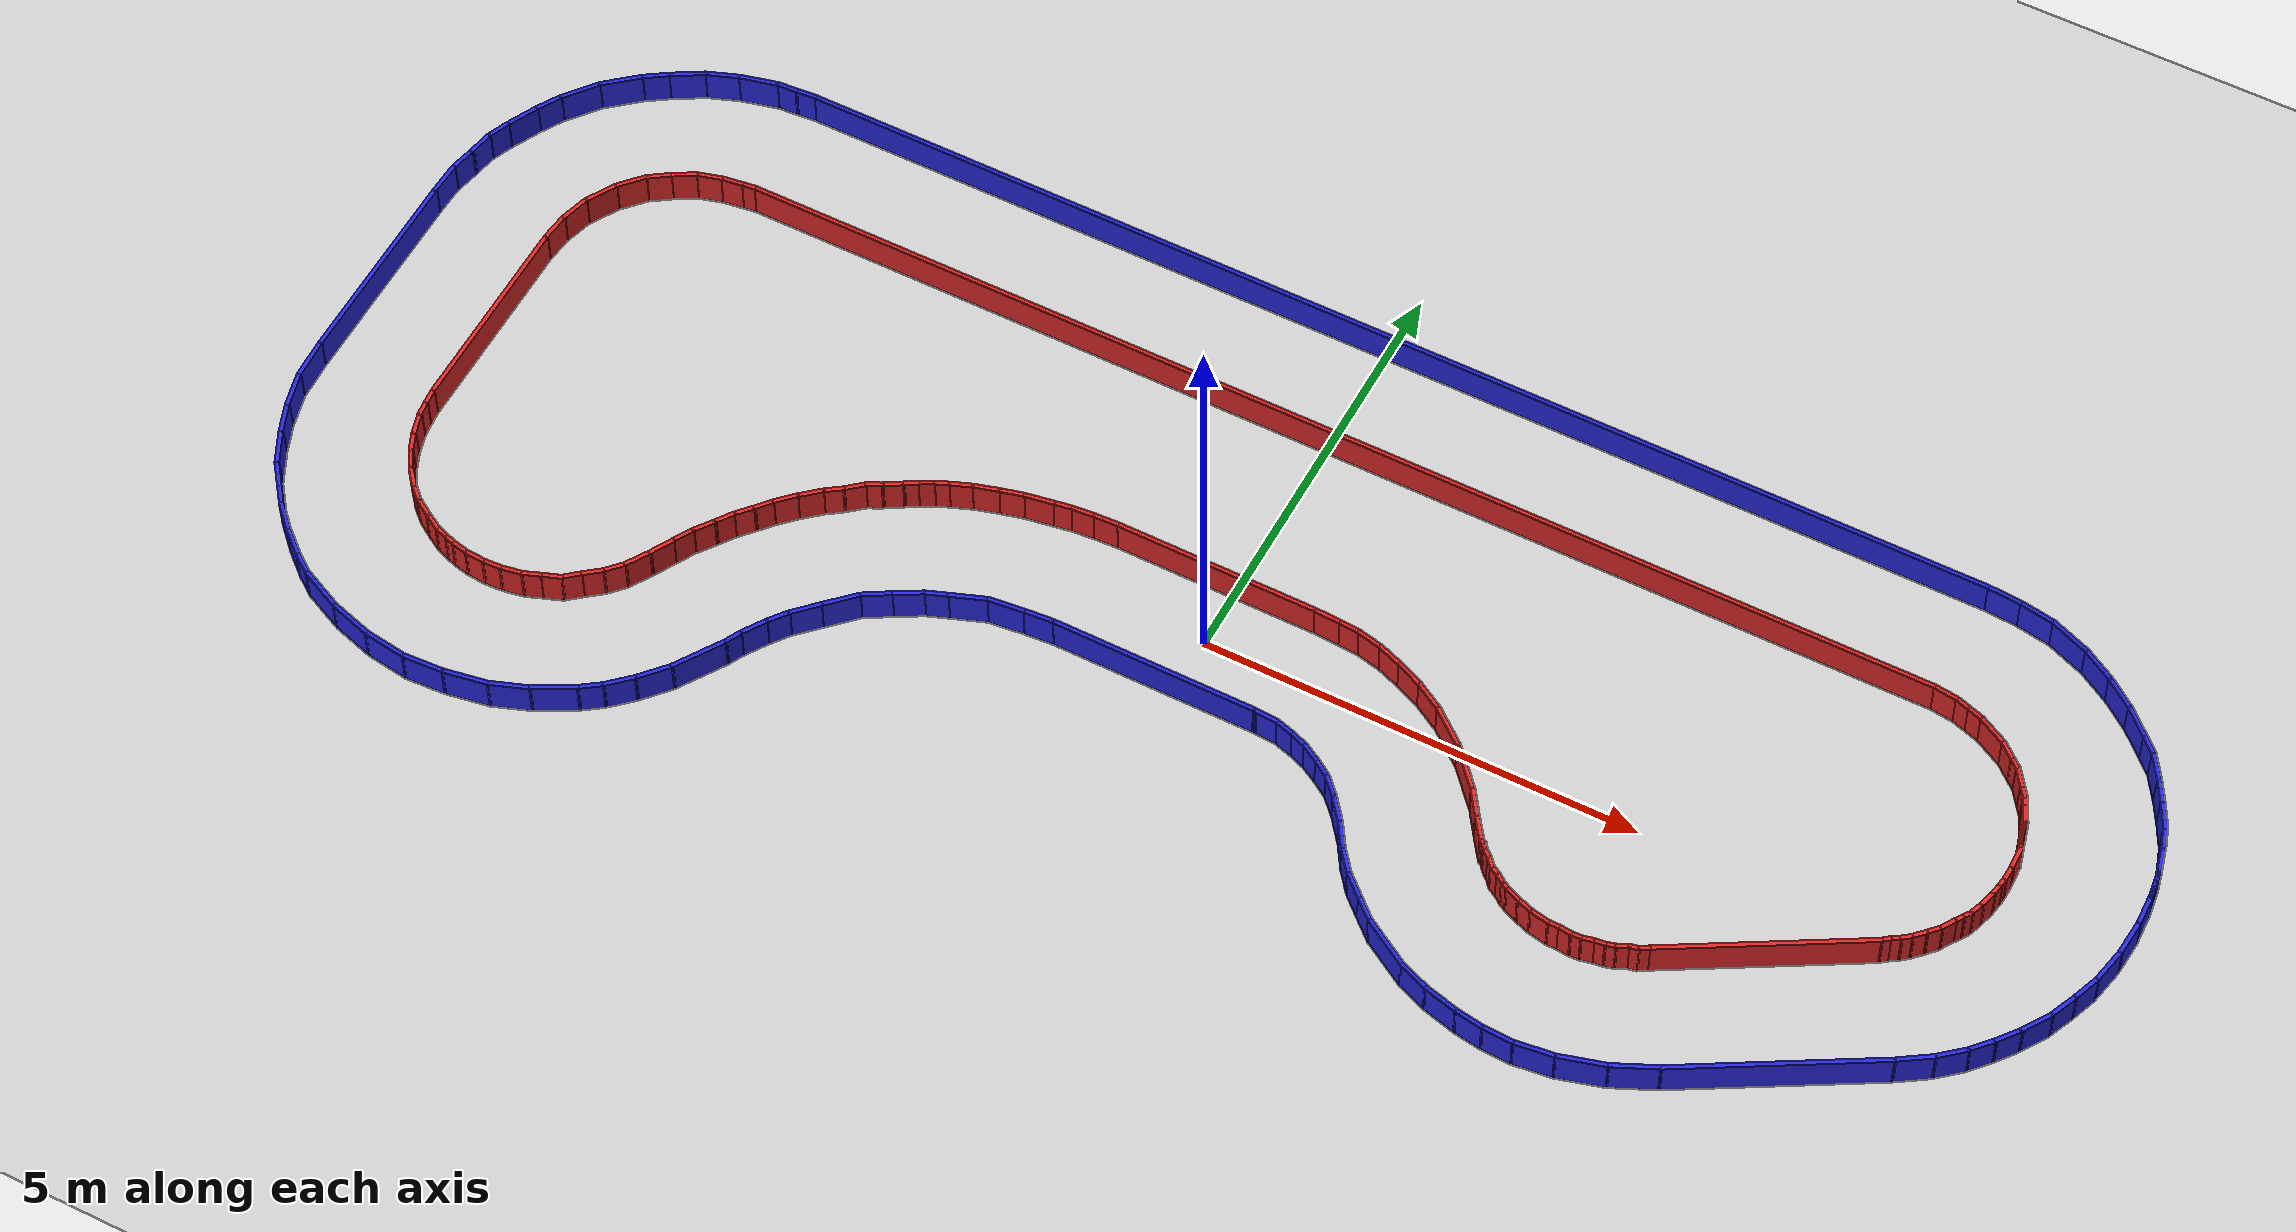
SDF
<?xml version="1.0"?>
<sdf version='1.8'>
    <world name='warehouse'>
        <physics name='1ms' type='ignored'>
            <max_step_size>0.003</max_step_size>
            <real_time_factor>1</real_time_factor>
            <real_time_update_rate>1000</real_time_update_rate>
        </physics>
        <plugin name='ignition::gazebo::systems::Physics' filename='ignition-gazebo-physics-system' />
        <plugin name='ignition::gazebo::systems::UserCommands' filename='ignition-gazebo-user-commands-system' />
        <plugin name='ignition::gazebo::systems::SceneBroadcaster' filename='ignition-gazebo-scene-broadcaster-system' />
        <plugin name='ignition::gazebo::systems::Contact' filename='ignition-gazebo-contact-system' />
        <light name='sun' type='directional'>
            <cast_shadows>1</cast_shadows>
            <pose>0 0 10 0 -0 0</pose>
            <diffuse>0.8 0.8 0.8 1</diffuse>
            <specular>0.2 0.2 0.2 1</specular>
            <attenuation>
                <range>1000</range>
                <constant>0.90000000000000002</constant>
                <linear>0.01</linear>
                <quadratic>0.001</quadratic>
            </attenuation>
            <direction>-0.5 0.1 -0.9</direction>
            <spot><inner_angle>0</inner_angle><outer_angle>0</outer_angle><falloff>0</falloff></spot>
        </light>
        <gravity>0 0 -9.8</gravity>
        <magnetic_field>6e-06 2.3e-05 -4.2e-05</magnetic_field>
        <atmosphere type='adiabatic' />
        <scene>
            <ambient>0.4 0.4 0.4 1</ambient>
            <background>0.7 0.7 0.7 1</background>
            <shadows>1</shadows>
        </scene>
        <model name='ground_plane'>
            <static>1</static>
            <link name='link'>
                <collision name='collision'>
                    <geometry><plane><normal>0 0 1</normal><size>100 100</size></plane></geometry>
                    <surface><friction><ode /></friction><bounce /><contact /></surface>
                </collision>
                <visual name='visual'>
                    <geometry><plane><normal>0 0 1</normal><size>100 100</size></plane></geometry>
                    <material>
                        <ambient>0.8 0.8 0.8 1</ambient>
                        <diffuse>0.8 0.8 0.8 1</diffuse>
                        <specular>0.8 0.8 0.8 1</specular>
                    </material>
                    <plugin name='__default__' filename='__default__' />
                </visual>
            </link>
            <plugin name='__default__' filename='__default__' />
            <pose>0 0 0 0 -0 0</pose>
        </model>

        <model name='outer_wall'>
            <pose>0 0 0 0 0 0</pose>
            <static>true</static>
            <link name='ow_0'>
                <pose>0.029010 2.797262 0.2000 0 0 0.000168</pose>
                <collision name='ow_0_collision'>
                    <geometry>
                        <box>
                            <size>13.991454 0.05 0.4</size>
                        </box>
                    </geometry>
                </collision>
                <visual name='ow_0_visual'>
                    <geometry>
                        <box>
                            <size>13.991454 0.05 0.4</size>
                        </box>
                    </geometry>
                    <material>
                        <ambient>0.85 0.15 0.15 1</ambient>
                        <diffuse>0.85 0.15 0.15 1</diffuse>
                        <specular>0.1 0.1 0.1 1</specular>
                    </material>
                </visual>
            </link>
            <link name='ow_1'>
                <pose>7.146808 2.782594 0.2000 0 0 -0.119394</pose>
                <collision name='ow_1_collision'>
                    <geometry>
                        <box>
                            <size>0.286036 0.05 0.4</size>
                        </box>
                    </geometry>
                </collision>
                <visual name='ow_1_visual'>
                    <geometry>
                        <box>
                            <size>0.286036 0.05 0.4</size>
                        </box>
                    </geometry>
                    <material>
                        <ambient>0.85 0.15 0.15 1</ambient>
                        <diffuse>0.85 0.15 0.15 1</diffuse>
                        <specular>0.1 0.1 0.1 1</specular>
                    </material>
                </visual>
            </link>
            <link name='ow_2'>
                <pose>7.358935 2.741938 0.2000 0 0 -0.300553</pose>
                <collision name='ow_2_collision'>
                    <geometry>
                        <box>
                            <size>0.187626 0.05 0.4</size>
                        </box>
                    </geometry>
                </collision>
                <visual name='ow_2_visual'>
                    <geometry>
                        <box>
                            <size>0.187626 0.05 0.4</size>
                        </box>
                    </geometry>
                    <material>
                        <ambient>0.85 0.15 0.15 1</ambient>
                        <diffuse>0.85 0.15 0.15 1</diffuse>
                        <specular>0.1 0.1 0.1 1</specular>
                    </material>
                </visual>
            </link>
            <link name='ow_3'>
                <pose>7.523251 2.690500 0.2000 0 0 -0.306055</pose>
                <collision name='ow_3_collision'>
                    <geometry>
                        <box>
                            <size>0.196733 0.05 0.4</size>
                        </box>
                    </geometry>
                </collision>
                <visual name='ow_3_visual'>
                    <geometry>
                        <box>
                            <size>0.196733 0.05 0.4</size>
                        </box>
                    </geometry>
                    <material>
                        <ambient>0.85 0.15 0.15 1</ambient>
                        <diffuse>0.85 0.15 0.15 1</diffuse>
                        <specular>0.1 0.1 0.1 1</specular>
                    </material>
                </visual>
            </link>
            <link name='ow_4'>
                <pose>7.765473 2.579333 0.2000 0 0 -0.491412</pose>
                <collision name='ow_4_collision'>
                    <geometry>
                        <box>
                            <size>0.378326 0.05 0.4</size>
                        </box>
                    </geometry>
                </collision>
                <visual name='ow_4_visual'>
                    <geometry>
                        <box>
                            <size>0.378326 0.05 0.4</size>
                        </box>
                    </geometry>
                    <material>
                        <ambient>0.85 0.15 0.15 1</ambient>
                        <diffuse>0.85 0.15 0.15 1</diffuse>
                        <specular>0.1 0.1 0.1 1</specular>
                    </material>
                </visual>
            </link>
            <link name='ow_5'>
                <pose>8.007550 2.422824 0.2000 0 0 -0.707728</pose>
                <collision name='ow_5_collision'>
                    <geometry>
                        <box>
                            <size>0.241401 0.05 0.4</size>
                        </box>
                    </geometry>
                </collision>
                <visual name='ow_5_visual'>
                    <geometry>
                        <box>
                            <size>0.241401 0.05 0.4</size>
                        </box>
                    </geometry>
                    <material>
                        <ambient>0.85 0.15 0.15 1</ambient>
                        <diffuse>0.85 0.15 0.15 1</diffuse>
                        <specular>0.1 0.1 0.1 1</specular>
                    </material>
                </visual>
            </link>
            <link name='ow_6'>
                <pose>8.137835 2.312118 0.2000 0 0 -0.698098</pose>
                <collision name='ow_6_collision'>
                    <geometry>
                        <box>
                            <size>0.140538 0.05 0.4</size>
                        </box>
                    </geometry>
                </collision>
                <visual name='ow_6_visual'>
                    <geometry>
                        <box>
                            <size>0.140538 0.05 0.4</size>
                        </box>
                    </geometry>
                    <material>
                        <ambient>0.85 0.15 0.15 1</ambient>
                        <diffuse>0.85 0.15 0.15 1</diffuse>
                        <specular>0.1 0.1 0.1 1</specular>
                    </material>
                </visual>
            </link>
            <link name='ow_7'>
                <pose>8.249366 2.182293 0.2000 0 0 -0.948377</pose>
                <collision name='ow_7_collision'>
                    <geometry>
                        <box>
                            <size>0.244221 0.05 0.4</size>
                        </box>
                    </geometry>
                </collision>
                <visual name='ow_7_visual'>
                    <geometry>
                        <box>
                            <size>0.244221 0.05 0.4</size>
                        </box>
                    </geometry>
                    <material>
                        <ambient>0.85 0.15 0.15 1</ambient>
                        <diffuse>0.85 0.15 0.15 1</diffuse>
                        <specular>0.1 0.1 0.1 1</specular>
                    </material>
                </visual>
            </link>
            <link name='ow_8'>
                <pose>8.351868 2.039847 0.2000 0 0 -0.944688</pose>
                <collision name='ow_8_collision'>
                    <geometry>
                        <box>
                            <size>0.146764 0.05 0.4</size>
                        </box>
                    </geometry>
                </collision>
                <visual name='ow_8_visual'>
                    <geometry>
                        <box>
                            <size>0.146764 0.05 0.4</size>
                        </box>
                    </geometry>
                    <material>
                        <ambient>0.85 0.15 0.15 1</ambient>
                        <diffuse>0.85 0.15 0.15 1</diffuse>
                        <specular>0.1 0.1 0.1 1</specular>
                    </material>
                </visual>
            </link>
            <link name='ow_9'>
                <pose>8.410924 1.937092 0.2000 0 0 -1.167752</pose>
                <collision name='ow_9_collision'>
                    <geometry>
                        <box>
                            <size>0.131746 0.05 0.4</size>
                        </box>
                    </geometry>
                </collision>
                <visual name='ow_9_visual'>
                    <geometry>
                        <box>
                            <size>0.131746 0.05 0.4</size>
                        </box>
                    </geometry>
                    <material>
                        <ambient>0.85 0.15 0.15 1</ambient>
                        <diffuse>0.85 0.15 0.15 1</diffuse>
                        <specular>0.1 0.1 0.1 1</specular>
                    </material>
                </visual>
            </link>
            <link name='ow_10'>
                <pose>8.473475 1.799167 0.2000 0 0 -1.131743</pose>
                <collision name='ow_10_collision'>
                    <geometry>
                        <box>
                            <size>0.211190 0.05 0.4</size>
                        </box>
                    </geometry>
                </collision>
                <visual name='ow_10_visual'>
                    <geometry>
                        <box>
                            <size>0.211190 0.05 0.4</size>
                        </box>
                    </geometry>
                    <material>
                        <ambient>0.85 0.15 0.15 1</ambient>
                        <diffuse>0.85 0.15 0.15 1</diffuse>
                        <specular>0.1 0.1 0.1 1</specular>
                    </material>
                </visual>
            </link>
            <link name='ow_11'>
                <pose>8.514258 1.712508 0.2000 0 0 -0.726146</pose>
                <collision name='ow_11_collision'>
                    <geometry>
                        <box>
                            <size>0.020393 0.05 0.4</size>
                        </box>
                    </geometry>
                </collision>
                <visual name='ow_11_visual'>
                    <geometry>
                        <box>
                            <size>0.020393 0.05 0.4</size>
                        </box>
                    </geometry>
                    <material>
                        <ambient>0.85 0.15 0.15 1</ambient>
                        <diffuse>0.85 0.15 0.15 1</diffuse>
                        <specular>0.1 0.1 0.1 1</specular>
                    </material>
                </visual>
            </link>
            <link name='ow_12'>
                <pose>8.514814 1.711983 0.2000 0 0 -0.766705</pose>
                <collision name='ow_12_collision'>
                    <geometry>
                        <box>
                            <size>0.021137 0.05 0.4</size>
                        </box>
                    </geometry>
                </collision>
                <visual name='ow_12_visual'>
                    <geometry>
                        <box>
                            <size>0.021137 0.05 0.4</size>
                        </box>
                    </geometry>
                    <material>
                        <ambient>0.85 0.15 0.15 1</ambient>
                        <diffuse>0.85 0.15 0.15 1</diffuse>
                        <specular>0.1 0.1 0.1 1</specular>
                    </material>
                </visual>
            </link>
            <link name='ow_13'>
                <pose>8.515847 1.710927 0.2000 0 0 -0.814986</pose>
                <collision name='ow_13_collision'>
                    <geometry>
                        <box>
                            <size>0.021818 0.05 0.4</size>
                        </box>
                    </geometry>
                </collision>
                <visual name='ow_13_visual'>
                    <geometry>
                        <box>
                            <size>0.021818 0.05 0.4</size>
                        </box>
                    </geometry>
                    <material>
                        <ambient>0.85 0.15 0.15 1</ambient>
                        <diffuse>0.85 0.15 0.15 1</diffuse>
                        <specular>0.1 0.1 0.1 1</specular>
                    </material>
                </visual>
            </link>
            <link name='ow_14'>
                <pose>8.517260 1.709333 0.2000 0 0 -0.868072</pose>
                <collision name='ow_14_collision'>
                    <geometry>
                        <box>
                            <size>0.022444 0.05 0.4</size>
                        </box>
                    </geometry>
                </collision>
                <visual name='ow_14_visual'>
                    <geometry>
                        <box>
                            <size>0.022444 0.05 0.4</size>
                        </box>
                    </geometry>
                    <material>
                        <ambient>0.85 0.15 0.15 1</ambient>
                        <diffuse>0.85 0.15 0.15 1</diffuse>
                        <specular>0.1 0.1 0.1 1</specular>
                    </material>
                </visual>
            </link>
            <link name='ow_15'>
                <pose>8.518958 1.707194 0.2000 0 0 -0.925843</pose>
                <collision name='ow_15_collision'>
                    <geometry>
                        <box>
                            <size>0.023020 0.05 0.4</size>
                        </box>
                    </geometry>
                </collision>
                <visual name='ow_15_visual'>
                    <geometry>
                        <box>
                            <size>0.023020 0.05 0.4</size>
                        </box>
                    </geometry>
                    <material>
                        <ambient>0.85 0.15 0.15 1</ambient>
                        <diffuse>0.85 0.15 0.15 1</diffuse>
                        <specular>0.1 0.1 0.1 1</specular>
                    </material>
                </visual>
            </link>
            <link name='ow_16'>
                <pose>8.520844 1.704502 0.2000 0 0 -0.988357</pose>
                <collision name='ow_16_collision'>
                    <geometry>
                        <box>
                            <size>0.023556 0.05 0.4</size>
                        </box>
                    </geometry>
                </collision>
                <visual name='ow_16_visual'>
                    <geometry>
                        <box>
                            <size>0.023556 0.05 0.4</size>
                        </box>
                    </geometry>
                    <material>
                        <ambient>0.85 0.15 0.15 1</ambient>
                        <diffuse>0.85 0.15 0.15 1</diffuse>
                        <specular>0.1 0.1 0.1 1</specular>
                    </material>
                </visual>
            </link>
            <link name='ow_17'>
                <pose>8.522822 1.701251 0.2000 0 0 -1.055611</pose>
                <collision name='ow_17_collision'>
                    <geometry>
                        <box>
                            <size>0.024060 0.05 0.4</size>
                        </box>
                    </geometry>
                </collision>
                <visual name='ow_17_visual'>
                    <geometry>
                        <box>
                            <size>0.024060 0.05 0.4</size>
                        </box>
                    </geometry>
                    <material>
                        <ambient>0.85 0.15 0.15 1</ambient>
                        <diffuse>0.85 0.15 0.15 1</diffuse>
                        <specular>0.1 0.1 0.1 1</specular>
                    </material>
                </visual>
            </link>
            <link name='ow_18'>
                <pose>8.524796 1.697433 0.2000 0 0 -1.127456</pose>
                <collision name='ow_18_collision'>
                    <geometry>
                        <box>
                            <size>0.024543 0.05 0.4</size>
                        </box>
                    </geometry>
                </collision>
                <visual name='ow_18_visual'>
                    <geometry>
                        <box>
                            <size>0.024543 0.05 0.4</size>
                        </box>
                    </geometry>
                    <material>
                        <ambient>0.85 0.15 0.15 1</ambient>
                        <diffuse>0.85 0.15 0.15 1</diffuse>
                        <specular>0.1 0.1 0.1 1</specular>
                    </material>
                </visual>
            </link>
            <link name='ow_19'>
                <pose>8.526671 1.693040 0.2000 0 0 -1.203547</pose>
                <collision name='ow_19_collision'>
                    <geometry>
                        <box>
                            <size>0.025016 0.05 0.4</size>
                        </box>
                    </geometry>
                </collision>
                <visual name='ow_19_visual'>
                    <geometry>
                        <box>
                            <size>0.025016 0.05 0.4</size>
                        </box>
                    </geometry>
                    <material>
                        <ambient>0.85 0.15 0.15 1</ambient>
                        <diffuse>0.85 0.15 0.15 1</diffuse>
                        <specular>0.1 0.1 0.1 1</specular>
                    </material>
                </visual>
            </link>
            <link name='ow_20'>
                <pose>8.528350 1.688067 0.2000 0 0 -1.283308</pose>
                <collision name='ow_20_collision'>
                    <geometry>
                        <box>
                            <size>0.025491 0.05 0.4</size>
                        </box>
                    </geometry>
                </collision>
                <visual name='ow_20_visual'>
                    <geometry>
                        <box>
                            <size>0.025491 0.05 0.4</size>
                        </box>
                    </geometry>
                    <material>
                        <ambient>0.85 0.15 0.15 1</ambient>
                        <diffuse>0.85 0.15 0.15 1</diffuse>
                        <specular>0.1 0.1 0.1 1</specular>
                    </material>
                </visual>
            </link>
            <link name='ow_21'>
                <pose>8.529737 1.682505 0.2000 0 0 -1.365927</pose>
                <collision name='ow_21_collision'>
                    <geometry>
                        <box>
                            <size>0.025983 0.05 0.4</size>
                        </box>
                    </geometry>
                </collision>
                <visual name='ow_21_visual'>
                    <geometry>
                        <box>
                            <size>0.025983 0.05 0.4</size>
                        </box>
                    </geometry>
                    <material>
                        <ambient>0.85 0.15 0.15 1</ambient>
                        <diffuse>0.85 0.15 0.15 1</diffuse>
                        <specular>0.1 0.1 0.1 1</specular>
                    </material>
                </visual>
            </link>
            <link name='ow_22'>
                <pose>8.530736 1.676348 0.2000 0 0 -1.450381</pose>
                <collision name='ow_22_collision'>
                    <geometry>
                        <box>
                            <size>0.026504 0.05 0.4</size>
                        </box>
                    </geometry>
                </collision>
                <visual name='ow_22_visual'>
                    <geometry>
                        <box>
                            <size>0.026504 0.05 0.4</size>
                        </box>
                    </geometry>
                    <material>
                        <ambient>0.85 0.15 0.15 1</ambient>
                        <diffuse>0.85 0.15 0.15 1</diffuse>
                        <specular>0.1 0.1 0.1 1</specular>
                    </material>
                </visual>
            </link>
            <link name='ow_23'>
                <pose>8.531392 1.669507 0.2000 0 0 -1.497422</pose>
                <collision name='ow_23_collision'>
                    <geometry>
                        <box>
                            <size>0.027244 0.05 0.4</size>
                        </box>
                    </geometry>
                </collision>
                <visual name='ow_23_visual'>
                    <geometry>
                        <box>
                            <size>0.027244 0.05 0.4</size>
                        </box>
                    </geometry>
                    <material>
                        <ambient>0.85 0.15 0.15 1</ambient>
                        <diffuse>0.85 0.15 0.15 1</diffuse>
                        <specular>0.1 0.1 0.1 1</specular>
                    </material>
                </visual>
            </link>
            <link name='ow_24'>
                <pose>8.531924 1.661882 0.2000 0 0 -1.504713</pose>
                <collision name='ow_24_collision'>
                    <geometry>
                        <box>
                            <size>0.028042 0.05 0.4</size>
                        </box>
                    </geometry>
                </collision>
                <visual name='ow_24_visual'>
                    <geometry>
                        <box>
                            <size>0.028042 0.05 0.4</size>
                        </box>
                    </geometry>
                    <material>
                        <ambient>0.85 0.15 0.15 1</ambient>
                        <diffuse>0.85 0.15 0.15 1</diffuse>
                        <specular>0.1 0.1 0.1 1</specular>
                    </material>
                </visual>
            </link>
            <link name='ow_25'>
                <pose>8.532455 1.653556 0.2000 0 0 -1.509314</pose>
                <collision name='ow_25_collision'>
                    <geometry>
                        <box>
                            <size>0.028644 0.05 0.4</size>
                        </box>
                    </geometry>
                </collision>
                <visual name='ow_25_visual'>
                    <geometry>
                        <box>
                            <size>0.028644 0.05 0.4</size>
                        </box>
                    </geometry>
                    <material>
                        <ambient>0.85 0.15 0.15 1</ambient>
                        <diffuse>0.85 0.15 0.15 1</diffuse>
                        <specular>0.1 0.1 0.1 1</specular>
                    </material>
                </visual>
            </link>
            <link name='ow_26'>
                <pose>8.532986 1.644726 0.2000 0 0 -1.512062</pose>
                <collision name='ow_26_collision'>
                    <geometry>
                        <box>
                            <size>0.029048 0.05 0.4</size>
                        </box>
                    </geometry>
                </collision>
                <visual name='ow_26_visual'>
                    <geometry>
                        <box>
                            <size>0.029048 0.05 0.4</size>
                        </box>
                    </geometry>
                    <material>
                        <ambient>0.85 0.15 0.15 1</ambient>
                        <diffuse>0.85 0.15 0.15 1</diffuse>
                        <specular>0.1 0.1 0.1 1</specular>
                    </material>
                </visual>
            </link>
            <link name='ow_27'>
                <pose>8.533517 1.635590 0.2000 0 0 -1.513374</pose>
                <collision name='ow_27_collision'>
                    <geometry>
                        <box>
                            <size>0.029255 0.05 0.4</size>
                        </box>
                    </geometry>
                </collision>
                <visual name='ow_27_visual'>
                    <geometry>
                        <box>
                            <size>0.029255 0.05 0.4</size>
                        </box>
                    </geometry>
                    <material>
                        <ambient>0.85 0.15 0.15 1</ambient>
                        <diffuse>0.85 0.15 0.15 1</diffuse>
                        <specular>0.1 0.1 0.1 1</specular>
                    </material>
                </visual>
            </link>
            <link name='ow_28'>
                <pose>8.534048 1.626346 0.2000 0 0 -1.513431</pose>
                <collision name='ow_28_collision'>
                    <geometry>
                        <box>
                            <size>0.029264 0.05 0.4</size>
                        </box>
                    </geometry>
                </collision>
                <visual name='ow_28_visual'>
                    <geometry>
                        <box>
                            <size>0.029264 0.05 0.4</size>
                        </box>
                    </geometry>
                    <material>
                        <ambient>0.85 0.15 0.15 1</ambient>
                        <diffuse>0.85 0.15 0.15 1</diffuse>
                        <specular>0.1 0.1 0.1 1</specular>
                    </material>
                </visual>
            </link>
            <link name='ow_29'>
                <pose>8.534579 1.617190 0.2000 0 0 -1.512241</pose>
                <collision name='ow_29_collision'>
                    <geometry>
                        <box>
                            <size>0.029077 0.05 0.4</size>
                        </box>
                    </geometry>
                </collision>
                <visual name='ow_29_visual'>
                    <geometry>
                        <box>
                            <size>0.029077 0.05 0.4</size>
                        </box>
                    </geometry>
                    <material>
                        <ambient>0.85 0.15 0.15 1</ambient>
                        <diffuse>0.85 0.15 0.15 1</diffuse>
                        <specular>0.1 0.1 0.1 1</specular>
                    </material>
                </visual>
            </link>
            <link name='ow_30'>
                <pose>8.535110 1.608322 0.2000 0 0 -1.509641</pose>
                <collision name='ow_30_collision'>
                    <geometry>
                        <box>
                            <size>0.028692 0.05 0.4</size>
                        </box>
                    </geometry>
                </collision>
                <visual name='ow_30_visual'>
                    <geometry>
                        <box>
                            <size>0.028692 0.05 0.4</size>
                        </box>
                    </geometry>
                    <material>
                        <ambient>0.85 0.15 0.15 1</ambient>
                        <diffuse>0.85 0.15 0.15 1</diffuse>
                        <specular>0.1 0.1 0.1 1</specular>
                    </material>
                </visual>
            </link>
            <link name='ow_31'>
                <pose>8.535642 1.599937 0.2000 0 0 -1.505243</pose>
                <collision name='ow_31_collision'>
                    <geometry>
                        <box>
                            <size>0.028111 0.05 0.4</size>
                        </box>
                    </geometry>
                </collision>
                <visual name='ow_31_visual'>
                    <geometry>
                        <box>
                            <size>0.028111 0.05 0.4</size>
                        </box>
                    </geometry>
                    <material>
                        <ambient>0.85 0.15 0.15 1</ambient>
                        <diffuse>0.85 0.15 0.15 1</diffuse>
                        <specular>0.1 0.1 0.1 1</specular>
                    </material>
                </visual>
            </link>
            <link name='ow_32'>
                <pose>8.536173 1.592234 0.2000 0 0 -1.498263</pose>
                <collision name='ow_32_collision'>
                    <geometry>
                        <box>
                            <size>0.027332 0.05 0.4</size>
                        </box>
                    </geometry>
                </collision>
                <visual name='ow_32_visual'>
                    <geometry>
                        <box>
                            <size>0.027332 0.05 0.4</size>
                        </box>
                    </geometry>
                    <material>
                        <ambient>0.85 0.15 0.15 1</ambient>
                        <diffuse>0.85 0.15 0.15 1</diffuse>
                        <specular>0.1 0.1 0.1 1</specular>
                    </material>
                </visual>
            </link>
            <link name='ow_33'>
                <pose>8.536704 1.585410 0.2000 0 0 -1.487103</pose>
                <collision name='ow_33_collision'>
                    <geometry>
                        <box>
                            <size>0.026357 0.05 0.4</size>
                        </box>
                    </geometry>
                </collision>
                <visual name='ow_33_visual'>
                    <geometry>
                        <box>
                            <size>0.026357 0.05 0.4</size>
                        </box>
                    </geometry>
                    <material>
                        <ambient>0.85 0.15 0.15 1</ambient>
                        <diffuse>0.85 0.15 0.15 1</diffuse>
                        <specular>0.1 0.1 0.1 1</specular>
                    </material>
                </visual>
            </link>
            <link name='ow_34'>
                <pose>8.537236 1.579663 0.2000 0 0 -1.468142</pose>
                <collision name='ow_34_collision'>
                    <geometry>
                        <box>
                            <size>0.025186 0.05 0.4</size>
                        </box>
                    </geometry>
                </collision>
                <visual name='ow_34_visual'>
                    <geometry>
                        <box>
                            <size>0.025186 0.05 0.4</size>
                        </box>
                    </geometry>
                    <material>
                        <ambient>0.85 0.15 0.15 1</ambient>
                        <diffuse>0.85 0.15 0.15 1</diffuse>
                        <specular>0.1 0.1 0.1 1</specular>
                    </material>
                </visual>
            </link>
            <link name='ow_35'>
                <pose>8.538376 1.573562 0.2000 0 0 -1.327310</pose>
                <collision name='ow_35_collision'>
                    <geometry>
                        <box>
                            <size>0.027257 0.05 0.4</size>
                        </box>
                    </geometry>
                </collision>
                <visual name='ow_35_visual'>
                    <geometry>
                        <box>
                            <size>0.027257 0.05 0.4</size>
                        </box>
                    </geometry>
                    <material>
                        <ambient>0.85 0.15 0.15 1</ambient>
                        <diffuse>0.85 0.15 0.15 1</diffuse>
                        <specular>0.1 0.1 0.1 1</specular>
                    </material>
                </visual>
            </link>
            <link name='ow_36'>
                <pose>8.541198 1.564303 0.2000 0 0 -1.243636</pose>
                <collision name='ow_36_collision'>
                    <geometry>
                        <box>
                            <size>0.032119 0.05 0.4</size>
                        </box>
                    </geometry>
                </collision>
                <visual name='ow_36_visual'>
                    <geometry>
                        <box>
                            <size>0.032119 0.05 0.4</size>
                        </box>
                    </geometry>
                    <material>
                        <ambient>0.85 0.15 0.15 1</ambient>
                        <diffuse>0.85 0.15 0.15 1</diffuse>
                        <specular>0.1 0.1 0.1 1</specular>
                    </material>
                </visual>
            </link>
            <link name='ow_37'>
                <pose>8.545947 1.551090 0.2000 0 0 -1.212249</pose>
                <collision name='ow_37_collision'>
                    <geometry>
                        <box>
                            <size>0.035964 0.05 0.4</size>
                        </box>
                    </geometry>
                </collision>
                <visual name='ow_37_visual'>
                    <geometry>
                        <box>
                            <size>0.035964 0.05 0.4</size>
                        </box>
                    </geometry>
                    <material>
                        <ambient>0.85 0.15 0.15 1</ambient>
                        <diffuse>0.85 0.15 0.15 1</diffuse>
                        <specular>0.1 0.1 0.1 1</specular>
                    </material>
                </visual>
            </link>
            <link name='ow_38'>
                <pose>8.552183 1.534887 0.2000 0 0 -1.195842</pose>
                <collision name='ow_38_collision'>
                    <geometry>
                        <box>
                            <size>0.038762 0.05 0.4</size>
                        </box>
                    </geometry>
                </collision>
                <visual name='ow_38_visual'>
                    <geometry>
                        <box>
                            <size>0.038762 0.05 0.4</size>
                        </box>
                    </geometry>
                    <material>
                        <ambient>0.85 0.15 0.15 1</ambient>
                        <diffuse>0.85 0.15 0.15 1</diffuse>
                        <specular>0.1 0.1 0.1 1</specular>
                    </material>
                </visual>
            </link>
            <link name='ow_39'>
                <pose>8.559470 1.516654 0.2000 0 0 -1.185762</pose>
                <collision name='ow_39_collision'>
                    <geometry>
                        <box>
                            <size>0.040508 0.05 0.4</size>
                        </box>
                    </geometry>
                </collision>
                <visual name='ow_39_visual'>
                    <geometry>
                        <box>
                            <size>0.040508 0.05 0.4</size>
                        </box>
                    </geometry>
                    <material>
                        <ambient>0.85 0.15 0.15 1</ambient>
                        <diffuse>0.85 0.15 0.15 1</diffuse>
                        <specular>0.1 0.1 0.1 1</specular>
                    </material>
                </visual>
            </link>
            <link name='ow_40'>
                <pose>8.567370 1.497354 0.2000 0 0 -1.178943</pose>
                <collision name='ow_40_collision'>
                    <geometry>
                        <box>
                            <size>0.041200 0.05 0.4</size>
                        </box>
                    </geometry>
                </collision>
                <visual name='ow_40_visual'>
                    <geometry>
                        <box>
                            <size>0.041200 0.05 0.4</size>
                        </box>
                    </geometry>
                    <material>
                        <ambient>0.85 0.15 0.15 1</ambient>
                        <diffuse>0.85 0.15 0.15 1</diffuse>
                        <specular>0.1 0.1 0.1 1</specular>
                    </material>
                </visual>
            </link>
            <link name='ow_41'>
                <pose>8.575444 1.477949 0.2000 0 0 -1.174025</pose>
                <collision name='ow_41_collision'>
                    <geometry>
                        <box>
                            <size>0.040836 0.05 0.4</size>
                        </box>
                    </geometry>
                </collision>
                <visual name='ow_41_visual'>
                    <geometry>
                        <box>
                            <size>0.040836 0.05 0.4</size>
                        </box>
                    </geometry>
                    <material>
                        <ambient>0.85 0.15 0.15 1</ambient>
                        <diffuse>0.85 0.15 0.15 1</diffuse>
                        <specular>0.1 0.1 0.1 1</specular>
                    </material>
                </visual>
            </link>
            <link name='ow_42'>
                <pose>8.583255 1.459400 0.2000 0 0 -1.170311</pose>
                <collision name='ow_42_collision'>
                    <geometry>
                        <box>
                            <size>0.039417 0.05 0.4</size>
                        </box>
                    </geometry>
                </collision>
                <visual name='ow_42_visual'>
                    <geometry>
                        <box>
                            <size>0.039417 0.05 0.4</size>
                        </box>
                    </geometry>
                    <material>
                        <ambient>0.85 0.15 0.15 1</ambient>
                        <diffuse>0.85 0.15 0.15 1</diffuse>
                        <specular>0.1 0.1 0.1 1</specular>
                    </material>
                </visual>
            </link>
            <link name='ow_43'>
                <pose>8.590365 1.442669 0.2000 0 0 -1.167409</pose>
                <collision name='ow_43_collision'>
                    <geometry>
                        <box>
                            <size>0.036941 0.05 0.4</size>
                        </box>
                    </geometry>
                </collision>
                <visual name='ow_43_visual'>
                    <geometry>
                        <box>
                            <size>0.036941 0.05 0.4</size>
                        </box>
                    </geometry>
                    <material>
                        <ambient>0.85 0.15 0.15 1</ambient>
                        <diffuse>0.85 0.15 0.15 1</diffuse>
                        <specular>0.1 0.1 0.1 1</specular>
                    </material>
                </visual>
            </link>
            <link name='ow_44'>
                <pose>8.596336 1.428719 0.2000 0 0 -1.165085</pose>
                <collision name='ow_44_collision'>
                    <geometry>
                        <box>
                            <size>0.033409 0.05 0.4</size>
                        </box>
                    </geometry>
                </collision>
                <visual name='ow_44_visual'>
                    <geometry>
                        <box>
                            <size>0.033409 0.05 0.4</size>
                        </box>
                    </geometry>
                    <material>
                        <ambient>0.85 0.15 0.15 1</ambient>
                        <diffuse>0.85 0.15 0.15 1</diffuse>
                        <specular>0.1 0.1 0.1 1</specular>
                    </material>
                </visual>
            </link>
            <link name='ow_45'>
                <pose>8.600730 1.418510 0.2000 0 0 -1.163196</pose>
                <collision name='ow_45_collision'>
                    <geometry>
                        <box>
                            <size>0.028820 0.05 0.4</size>
                        </box>
                    </geometry>
                </collision>
                <visual name='ow_45_visual'>
                    <geometry>
                        <box>
                            <size>0.028820 0.05 0.4</size>
                        </box>
                    </geometry>
                    <material>
                        <ambient>0.85 0.15 0.15 1</ambient>
                        <diffuse>0.85 0.15 0.15 1</diffuse>
                        <specular>0.1 0.1 0.1 1</specular>
                    </material>
                </visual>
            </link>
            <link name='ow_46'>
                <pose>8.603109 1.413005 0.2000 0 0 -1.161746</pose>
                <collision name='ow_46_collision'>
                    <geometry>
                        <box>
                            <size>0.023175 0.05 0.4</size>
                        </box>
                    </geometry>
                </collision>
                <visual name='ow_46_visual'>
                    <geometry>
                        <box>
                            <size>0.023175 0.05 0.4</size>
                        </box>
                    </geometry>
                    <material>
                        <ambient>0.85 0.15 0.15 1</ambient>
                        <diffuse>0.85 0.15 0.15 1</diffuse>
                        <specular>0.1 0.1 0.1 1</specular>
                    </material>
                </visual>
            </link>
            <link name='ow_47'>
                <pose>8.610303 1.272179 0.2000 0 0 -1.523743</pose>
                <collision name='ow_47_collision'>
                    <geometry>
                        <box>
                            <size>0.299048 0.05 0.4</size>
                        </box>
                    </geometry>
                </collision>
                <visual name='ow_47_visual'>
                    <geometry>
                        <box>
                            <size>0.299048 0.05 0.4</size>
                        </box>
                    </geometry>
                    <material>
                        <ambient>0.85 0.15 0.15 1</ambient>
                        <diffuse>0.85 0.15 0.15 1</diffuse>
                        <specular>0.1 0.1 0.1 1</specular>
                    </material>
                </visual>
            </link>
            <link name='ow_48'>
                <pose>8.613793 1.051434 0.2000 0 0 -1.608541</pose>
                <collision name='ow_48_collision'>
                    <geometry>
                        <box>
                            <size>0.182866 0.05 0.4</size>
                        </box>
                    </geometry>
                </collision>
                <visual name='ow_48_visual'>
                    <geometry>
                        <box>
                            <size>0.182866 0.05 0.4</size>
                        </box>
                    </geometry>
                    <material>
                        <ambient>0.85 0.15 0.15 1</ambient>
                        <diffuse>0.85 0.15 0.15 1</diffuse>
                        <specular>0.1 0.1 0.1 1</specular>
                    </material>
                </visual>
            </link>
            <link name='ow_49'>
                <pose>8.604440 0.934363 0.2000 0 0 -1.744938</pose>
                <collision name='ow_49_collision'>
                    <geometry>
                        <box>
                            <size>0.092488 0.05 0.4</size>
                        </box>
                    </geometry>
                </collision>
                <visual name='ow_49_visual'>
                    <geometry>
                        <box>
                            <size>0.092488 0.05 0.4</size>
                        </box>
                    </geometry>
                    <material>
                        <ambient>0.85 0.15 0.15 1</ambient>
                        <diffuse>0.85 0.15 0.15 1</diffuse>
                        <specular>0.1 0.1 0.1 1</specular>
                    </material>
                </visual>
            </link>
            <link name='ow_50'>
                <pose>8.587956 0.835043 0.2000 0 0 -1.729836</pose>
                <collision name='ow_50_collision'>
                    <geometry>
                        <box>
                            <size>0.148873 0.05 0.4</size>
                        </box>
                    </geometry>
                </collision>
                <visual name='ow_50_visual'>
                    <geometry>
                        <box>
                            <size>0.148873 0.05 0.4</size>
                        </box>
                    </geometry>
                    <material>
                        <ambient>0.85 0.15 0.15 1</ambient>
                        <diffuse>0.85 0.15 0.15 1</diffuse>
                        <specular>0.1 0.1 0.1 1</specular>
                    </material>
                </visual>
            </link>
            <link name='ow_51'>
                <pose>8.554089 0.686080 0.2000 0 0 -1.841268</pose>
                <collision name='ow_51_collision'>
                    <geometry>
                        <box>
                            <size>0.197119 0.05 0.4</size>
                        </box>
                    </geometry>
                </collision>
                <visual name='ow_51_visual'>
                    <geometry>
                        <box>
                            <size>0.197119 0.05 0.4</size>
                        </box>
                    </geometry>
                    <material>
                        <ambient>0.85 0.15 0.15 1</ambient>
                        <diffuse>0.85 0.15 0.15 1</diffuse>
                        <specular>0.1 0.1 0.1 1</specular>
                    </material>
                </visual>
            </link>
            <link name='ow_52'>
                <pose>8.504578 0.531661 0.2000 0 0 -1.928867</pose>
                <collision name='ow_52_collision'>
                    <geometry>
                        <box>
                            <size>0.167514 0.05 0.4</size>
                        </box>
                    </geometry>
                </collision>
                <visual name='ow_52_visual'>
                    <geometry>
                        <box>
                            <size>0.167514 0.05 0.4</size>
                        </box>
                    </geometry>
                    <material>
                        <ambient>0.85 0.15 0.15 1</ambient>
                        <diffuse>0.85 0.15 0.15 1</diffuse>
                        <specular>0.1 0.1 0.1 1</specular>
                    </material>
                </visual>
            </link>
            <link name='ow_53'>
                <pose>8.451132 0.420265 0.2000 0 0 -2.148658</pose>
                <collision name='ow_53_collision'>
                    <geometry>
                        <box>
                            <size>0.121040 0.05 0.4</size>
                        </box>
                    </geometry>
                </collision>
                <visual name='ow_53_visual'>
                    <geometry>
                        <box>
                            <size>0.121040 0.05 0.4</size>
                        </box>
                    </geometry>
                    <material>
                        <ambient>0.85 0.15 0.15 1</ambient>
                        <diffuse>0.85 0.15 0.15 1</diffuse>
                        <specular>0.1 0.1 0.1 1</specular>
                    </material>
                </visual>
            </link>
            <link name='ow_54'>
                <pose>8.397176 0.341059 0.2000 0 0 -2.191264</pose>
                <collision name='ow_54_collision'>
                    <geometry>
                        <box>
                            <size>0.110679 0.05 0.4</size>
                        </box>
                    </geometry>
                </collision>
                <visual name='ow_54_visual'>
                    <geometry>
                        <box>
                            <size>0.110679 0.05 0.4</size>
                        </box>
                    </geometry>
                    <material>
                        <ambient>0.85 0.15 0.15 1</ambient>
                        <diffuse>0.85 0.15 0.15 1</diffuse>
                        <specular>0.1 0.1 0.1 1</specular>
                    </material>
                </visual>
            </link>
            <link name='ow_55'>
                <pose>8.326747 0.232820 0.2000 0 0 -2.124067</pose>
                <collision name='ow_55_collision'>
                    <geometry>
                        <box>
                            <size>0.187723 0.05 0.4</size>
                        </box>
                    </geometry>
                </collision>
                <visual name='ow_55_visual'>
                    <geometry>
                        <box>
                            <size>0.187723 0.05 0.4</size>
                        </box>
                    </geometry>
                    <material>
                        <ambient>0.85 0.15 0.15 1</ambient>
                        <diffuse>0.85 0.15 0.15 1</diffuse>
                        <specular>0.1 0.1 0.1 1</specular>
                    </material>
                </visual>
            </link>
            <link name='ow_56'>
                <pose>8.227238 0.101280 0.2000 0 0 -2.315158</pose>
                <collision name='ow_56_collision'>
                    <geometry>
                        <box>
                            <size>0.183666 0.05 0.4</size>
                        </box>
                    </geometry>
                </collision>
                <visual name='ow_56_visual'>
                    <geometry>
                        <box>
                            <size>0.183666 0.05 0.4</size>
                        </box>
                    </geometry>
                    <material>
                        <ambient>0.85 0.15 0.15 1</ambient>
                        <diffuse>0.85 0.15 0.15 1</diffuse>
                        <specular>0.1 0.1 0.1 1</specular>
                    </material>
                </visual>
            </link>
            <link name='ow_57'>
                <pose>8.117167 -0.014267 0.2000 0 0 -2.349579</pose>
                <collision name='ow_57_collision'>
                    <geometry>
                        <box>
                            <size>0.175547 0.05 0.4</size>
                        </box>
                    </geometry>
                </collision>
                <visual name='ow_57_visual'>
                    <geometry>
                        <box>
                            <size>0.175547 0.05 0.4</size>
                        </box>
                    </geometry>
                    <material>
                        <ambient>0.85 0.15 0.15 1</ambient>
                        <diffuse>0.85 0.15 0.15 1</diffuse>
                        <specular>0.1 0.1 0.1 1</specular>
                    </material>
                </visual>
            </link>
            <link name='ow_58'>
                <pose>8.018768 -0.103488 0.2000 0 0 -2.483094</pose>
                <collision name='ow_58_collision'>
                    <geometry>
                        <box>
                            <size>0.130681 0.05 0.4</size>
                        </box>
                    </geometry>
                </collision>
                <visual name='ow_58_visual'>
                    <geometry>
                        <box>
                            <size>0.130681 0.05 0.4</size>
                        </box>
                    </geometry>
                    <material>
                        <ambient>0.85 0.15 0.15 1</ambient>
                        <diffuse>0.85 0.15 0.15 1</diffuse>
                        <specular>0.1 0.1 0.1 1</specular>
                    </material>
                </visual>
            </link>
            <link name='ow_59'>
                <pose>7.929174 -0.165946 0.2000 0 0 -2.583741</pose>
                <collision name='ow_59_collision'>
                    <geometry>
                        <box>
                            <size>0.128027 0.05 0.4</size>
                        </box>
                    </geometry>
                </collision>
                <visual name='ow_59_visual'>
                    <geometry>
                        <box>
                            <size>0.128027 0.05 0.4</size>
                        </box>
                    </geometry>
                    <material>
                        <ambient>0.85 0.15 0.15 1</ambient>
                        <diffuse>0.85 0.15 0.15 1</diffuse>
                        <specular>0.1 0.1 0.1 1</specular>
                    </material>
                </visual>
            </link>
            <link name='ow_60'>
                <pose>7.846386 -0.223863 0.2000 0 0 -2.470929</pose>
                <collision name='ow_60_collision'>
                    <geometry>
                        <box>
                            <size>0.114365 0.05 0.4</size>
                        </box>
                    </geometry>
                </collision>
                <visual name='ow_60_visual'>
                    <geometry>
                        <box>
                            <size>0.114365 0.05 0.4</size>
                        </box>
                    </geometry>
                    <material>
                        <ambient>0.85 0.15 0.15 1</ambient>
                        <diffuse>0.85 0.15 0.15 1</diffuse>
                        <specular>0.1 0.1 0.1 1</specular>
                    </material>
                </visual>
            </link>
            <link name='ow_61'>
                <pose>6.800926 -0.835768 0.2000 0 0 -2.617752</pose>
                <collision name='ow_61_collision'>
                    <geometry>
                        <box>
                            <size>2.349350 0.05 0.4</size>
                        </box>
                    </geometry>
                </collision>
                <visual name='ow_61_visual'>
                    <geometry>
                        <box>
                            <size>2.349350 0.05 0.4</size>
                        </box>
                    </geometry>
                    <material>
                        <ambient>0.85 0.15 0.15 1</ambient>
                        <diffuse>0.85 0.15 0.15 1</diffuse>
                        <specular>0.1 0.1 0.1 1</specular>
                    </material>
                </visual>
            </link>
            <link name='ow_62'>
                <pose>5.748016 -1.446610 0.2000 0 0 -2.574871</pose>
                <collision name='ow_62_collision'>
                    <geometry>
                        <box>
                            <size>0.125283 0.05 0.4</size>
                        </box>
                    </geometry>
                </collision>
                <visual name='ow_62_visual'>
                    <geometry>
                        <box>
                            <size>0.125283 0.05 0.4</size>
                        </box>
                    </geometry>
                    <material>
                        <ambient>0.85 0.15 0.15 1</ambient>
                        <diffuse>0.85 0.15 0.15 1</diffuse>
                        <specular>0.1 0.1 0.1 1</specular>
                    </material>
                </visual>
            </link>
            <link name='ow_63'>
                <pose>5.653544 -1.485310 0.2000 0 0 -2.936028</pose>
                <collision name='ow_63_collision'>
                    <geometry>
                        <box>
                            <size>0.122275 0.05 0.4</size>
                        </box>
                    </geometry>
                </collision>
                <visual name='ow_63_visual'>
                    <geometry>
                        <box>
                            <size>0.122275 0.05 0.4</size>
                        </box>
                    </geometry>
                    <material>
                        <ambient>0.85 0.15 0.15 1</ambient>
                        <diffuse>0.85 0.15 0.15 1</diffuse>
                        <specular>0.1 0.1 0.1 1</specular>
                    </material>
                </visual>
            </link>
            <link name='ow_64'>
                <pose>5.544737 -1.525876 0.2000 0 0 -2.667722</pose>
                <collision name='ow_64_collision'>
                    <geometry>
                        <box>
                            <size>0.152043 0.05 0.4</size>
                        </box>
                    </geometry>
                </collision>
                <visual name='ow_64_visual'>
                    <geometry>
                        <box>
                            <size>0.152043 0.05 0.4</size>
                        </box>
                    </geometry>
                    <material>
                        <ambient>0.85 0.15 0.15 1</ambient>
                        <diffuse>0.85 0.15 0.15 1</diffuse>
                        <specular>0.1 0.1 0.1 1</specular>
                    </material>
                </visual>
            </link>
            <link name='ow_65'>
                <pose>5.433304 -1.570444 0.2000 0 0 -2.874092</pose>
                <collision name='ow_65_collision'>
                    <geometry>
                        <box>
                            <size>0.129259 0.05 0.4</size>
                        </box>
                    </geometry>
                </collision>
                <visual name='ow_65_visual'>
                    <geometry>
                        <box>
                            <size>0.129259 0.05 0.4</size>
                        </box>
                    </geometry>
                    <material>
                        <ambient>0.85 0.15 0.15 1</ambient>
                        <diffuse>0.85 0.15 0.15 1</diffuse>
                        <specular>0.1 0.1 0.1 1</specular>
                    </material>
                </visual>
            </link>
            <link name='ow_66'>
                <pose>5.325483 -1.591876 0.2000 0 0 -3.015431</pose>
                <collision name='ow_66_collision'>
                    <geometry>
                        <box>
                            <size>0.131153 0.05 0.4</size>
                        </box>
                    </geometry>
                </collision>
                <visual name='ow_66_visual'>
                    <geometry>
                        <box>
                            <size>0.131153 0.05 0.4</size>
                        </box>
                    </geometry>
                    <material>
                        <ambient>0.85 0.15 0.15 1</ambient>
                        <diffuse>0.85 0.15 0.15 1</diffuse>
                        <specular>0.1 0.1 0.1 1</specular>
                    </material>
                </visual>
            </link>
            <link name='ow_67'>
                <pose>5.202708 -1.613469 0.2000 0 0 -2.929005</pose>
                <collision name='ow_67_collision'>
                    <geometry>
                        <box>
                            <size>0.158396 0.05 0.4</size>
                        </box>
                    </geometry>
                </collision>
                <visual name='ow_67_visual'>
                    <geometry>
                        <box>
                            <size>0.158396 0.05 0.4</size>
                        </box>
                    </geometry>
                    <material>
                        <ambient>0.85 0.15 0.15 1</ambient>
                        <diffuse>0.85 0.15 0.15 1</diffuse>
                        <specular>0.1 0.1 0.1 1</specular>
                    </material>
                </visual>
            </link>
            <link name='ow_68'>
                <pose>5.079493 -1.631257 0.2000 0 0 -3.084303</pose>
                <collision name='ow_68_collision'>
                    <geometry>
                        <box>
                            <size>0.131332 0.05 0.4</size>
                        </box>
                    </geometry>
                </collision>
                <visual name='ow_68_visual'>
                    <geometry>
                        <box>
                            <size>0.131332 0.05 0.4</size>
                        </box>
                    </geometry>
                    <material>
                        <ambient>0.85 0.15 0.15 1</ambient>
                        <diffuse>0.85 0.15 0.15 1</diffuse>
                        <specular>0.1 0.1 0.1 1</specular>
                    </material>
                </visual>
            </link>
            <link name='ow_69'>
                <pose>4.951503 -1.626990 0.2000 0 0 3.039025</pose>
                <collision name='ow_69_collision'>
                    <geometry>
                        <box>
                            <size>0.165597 0.05 0.4</size>
                        </box>
                    </geometry>
                </collision>
                <visual name='ow_69_visual'>
                    <geometry>
                        <box>
                            <size>0.165597 0.05 0.4</size>
                        </box>
                    </geometry>
                    <material>
                        <ambient>0.85 0.15 0.15 1</ambient>
                        <diffuse>0.85 0.15 0.15 1</diffuse>
                        <specular>0.1 0.1 0.1 1</specular>
                    </material>
                </visual>
            </link>
            <link name='ow_70'>
                <pose>4.821139 -1.619537 0.2000 0 0 3.141593</pose>
                <collision name='ow_70_collision'>
                    <geometry>
                        <box>
                            <size>0.135895 0.05 0.4</size>
                        </box>
                    </geometry>
                </collision>
                <visual name='ow_70_visual'>
                    <geometry>
                        <box>
                            <size>0.135895 0.05 0.4</size>
                        </box>
                    </geometry>
                    <material>
                        <ambient>0.85 0.15 0.15 1</ambient>
                        <diffuse>0.85 0.15 0.15 1</diffuse>
                        <specular>0.1 0.1 0.1 1</specular>
                    </material>
                </visual>
            </link>
            <link name='ow_71'>
                <pose>4.656503 -1.599160 0.2000 0 0 2.952871</pose>
                <collision name='ow_71_collision'>
                    <geometry>
                        <box>
                            <size>0.237235 0.05 0.4</size>
                        </box>
                    </geometry>
                </collision>
                <visual name='ow_71_visual'>
                    <geometry>
                        <box>
                            <size>0.237235 0.05 0.4</size>
                        </box>
                    </geometry>
                    <material>
                        <ambient>0.85 0.15 0.15 1</ambient>
                        <diffuse>0.85 0.15 0.15 1</diffuse>
                        <specular>0.1 0.1 0.1 1</specular>
                    </material>
                </visual>
            </link>
            <link name='ow_72'>
                <pose>4.465679 -1.549882 0.2000 0 0 2.810709</pose>
                <collision name='ow_72_collision'>
                    <geometry>
                        <box>
                            <size>0.197920 0.05 0.4</size>
                        </box>
                    </geometry>
                </collision>
                <visual name='ow_72_visual'>
                    <geometry>
                        <box>
                            <size>0.197920 0.05 0.4</size>
                        </box>
                    </geometry>
                    <material>
                        <ambient>0.85 0.15 0.15 1</ambient>
                        <diffuse>0.85 0.15 0.15 1</diffuse>
                        <specular>0.1 0.1 0.1 1</specular>
                    </material>
                </visual>
            </link>
            <link name='ow_73'>
                <pose>4.302099 -1.487505 0.2000 0 0 2.742812</pose>
                <collision name='ow_73_collision'>
                    <geometry>
                        <box>
                            <size>0.192420 0.05 0.4</size>
                        </box>
                    </geometry>
                </collision>
                <visual name='ow_73_visual'>
                    <geometry>
                        <box>
                            <size>0.192420 0.05 0.4</size>
                        </box>
                    </geometry>
                    <material>
                        <ambient>0.85 0.15 0.15 1</ambient>
                        <diffuse>0.85 0.15 0.15 1</diffuse>
                        <specular>0.1 0.1 0.1 1</specular>
                    </material>
                </visual>
            </link>
            <link name='ow_74'>
                <pose>4.187053 -1.434073 0.2000 0 0 2.630646</pose>
                <collision name='ow_74_collision'>
                    <geometry>
                        <box>
                            <size>0.101627 0.05 0.4</size>
                        </box>
                    </geometry>
                </collision>
                <visual name='ow_74_visual'>
                    <geometry>
                        <box>
                            <size>0.101627 0.05 0.4</size>
                        </box>
                    </geometry>
                    <material>
                        <ambient>0.85 0.15 0.15 1</ambient>
                        <diffuse>0.85 0.15 0.15 1</diffuse>
                        <specular>0.1 0.1 0.1 1</specular>
                    </material>
                </visual>
            </link>
            <link name='ow_75'>
                <pose>4.106365 -1.380696 0.2000 0 0 2.503746</pose>
                <collision name='ow_75_collision'>
                    <geometry>
                        <box>
                            <size>0.132244 0.05 0.4</size>
                        </box>
                    </geometry>
                </collision>
                <visual name='ow_75_visual'>
                    <geometry>
                        <box>
                            <size>0.132244 0.05 0.4</size>
                        </box>
                    </geometry>
                    <material>
                        <ambient>0.85 0.15 0.15 1</ambient>
                        <diffuse>0.85 0.15 0.15 1</diffuse>
                        <specular>0.1 0.1 0.1 1</specular>
                    </material>
                </visual>
            </link>
            <link name='ow_76'>
                <pose>4.014897 -1.320321 0.2000 0 0 2.615118</pose>
                <collision name='ow_76_collision'>
                    <geometry>
                        <box>
                            <size>0.127290 0.05 0.4</size>
                        </box>
                    </geometry>
                </collision>
                <visual name='ow_76_visual'>
                    <geometry>
                        <box>
                            <size>0.127290 0.05 0.4</size>
                        </box>
                    </geometry>
                    <material>
                        <ambient>0.85 0.15 0.15 1</ambient>
                        <diffuse>0.85 0.15 0.15 1</diffuse>
                        <specular>0.1 0.1 0.1 1</specular>
                    </material>
                </visual>
            </link>
            <link name='ow_77'>
                <pose>3.930475 -1.250434 0.2000 0 0 2.295871</pose>
                <collision name='ow_77_collision'>
                    <geometry>
                        <box>
                            <size>0.134722 0.05 0.4</size>
                        </box>
                    </geometry>
                </collision>
                <visual name='ow_77_visual'>
                    <geometry>
                        <box>
                            <size>0.134722 0.05 0.4</size>
                        </box>
                    </geometry>
                    <material>
                        <ambient>0.85 0.15 0.15 1</ambient>
                        <diffuse>0.85 0.15 0.15 1</diffuse>
                        <specular>0.1 0.1 0.1 1</specular>
                    </material>
                </visual>
            </link>
            <link name='ow_78'>
                <pose>3.852966 -1.173173 0.2000 0 0 2.425712</pose>
                <collision name='ow_78_collision'>
                    <geometry>
                        <box>
                            <size>0.124617 0.05 0.4</size>
                        </box>
                    </geometry>
                </collision>
                <visual name='ow_78_visual'>
                    <geometry>
                        <box>
                            <size>0.124617 0.05 0.4</size>
                        </box>
                    </geometry>
                    <material>
                        <ambient>0.85 0.15 0.15 1</ambient>
                        <diffuse>0.85 0.15 0.15 1</diffuse>
                        <specular>0.1 0.1 0.1 1</specular>
                    </material>
                </visual>
            </link>
            <link name='ow_79'>
                <pose>3.791794 -1.110022 0.2000 0 0 2.216244</pose>
                <collision name='ow_79_collision'>
                    <geometry>
                        <box>
                            <size>0.092159 0.05 0.4</size>
                        </box>
                    </geometry>
                </collision>
                <visual name='ow_79_visual'>
                    <geometry>
                        <box>
                            <size>0.092159 0.05 0.4</size>
                        </box>
                    </geometry>
                    <material>
                        <ambient>0.85 0.15 0.15 1</ambient>
                        <diffuse>0.85 0.15 0.15 1</diffuse>
                        <specular>0.1 0.1 0.1 1</specular>
                    </material>
                </visual>
            </link>
            <link name='ow_80'>
                <pose>3.751130 -1.069153 0.2000 0 0 2.575580</pose>
                <collision name='ow_80_collision'>
                    <geometry>
                        <box>
                            <size>0.064928 0.05 0.4</size>
                        </box>
                    </geometry>
                </collision>
                <visual name='ow_80_visual'>
                    <geometry>
                        <box>
                            <size>0.064928 0.05 0.4</size>
                        </box>
                    </geometry>
                    <material>
                        <ambient>0.85 0.15 0.15 1</ambient>
                        <diffuse>0.85 0.15 0.15 1</diffuse>
                        <specular>0.1 0.1 0.1 1</specular>
                    </material>
                </visual>
            </link>
            <link name='ow_81'>
                <pose>3.649255 -0.941085 0.2000 0 0 2.191284</pose>
                <collision name='ow_81_collision'>
                    <geometry>
                        <box>
                            <size>0.305207 0.05 0.4</size>
                        </box>
                    </geometry>
                </collision>
                <visual name='ow_81_visual'>
                    <geometry>
                        <box>
                            <size>0.305207 0.05 0.4</size>
                        </box>
                    </geometry>
                    <material>
                        <ambient>0.85 0.15 0.15 1</ambient>
                        <diffuse>0.85 0.15 0.15 1</diffuse>
                        <specular>0.1 0.1 0.1 1</specular>
                    </material>
                </visual>
            </link>
            <link name='ow_82'>
                <pose>3.471512 -0.685414 0.2000 0 0 2.167322</pose>
                <collision name='ow_82_collision'>
                    <geometry>
                        <box>
                            <size>0.357605 0.05 0.4</size>
                        </box>
                    </geometry>
                </collision>
                <visual name='ow_82_visual'>
                    <geometry>
                        <box>
                            <size>0.357605 0.05 0.4</size>
                        </box>
                    </geometry>
                    <material>
                        <ambient>0.85 0.15 0.15 1</ambient>
                        <diffuse>0.85 0.15 0.15 1</diffuse>
                        <specular>0.1 0.1 0.1 1</specular>
                    </material>
                </visual>
            </link>
            <link name='ow_83'>
                <pose>3.192515 -0.339963 0.2000 0 0 2.300775</pose>
                <collision name='ow_83_collision'>
                    <geometry>
                        <box>
                            <size>0.572349 0.05 0.4</size>
                        </box>
                    </geometry>
                </collision>
                <visual name='ow_83_visual'>
                    <geometry>
                        <box>
                            <size>0.572349 0.05 0.4</size>
                        </box>
                    </geometry>
                    <material>
                        <ambient>0.85 0.15 0.15 1</ambient>
                        <diffuse>0.85 0.15 0.15 1</diffuse>
                        <specular>0.1 0.1 0.1 1</specular>
                    </material>
                </visual>
            </link>
            <link name='ow_84'>
                <pose>2.812937 0.023557 0.2000 0 0 2.462529</pose>
                <collision name='ow_84_collision'>
                    <geometry>
                        <box>
                            <size>0.522235 0.05 0.4</size>
                        </box>
                    </geometry>
                </collision>
                <visual name='ow_84_visual'>
                    <geometry>
                        <box>
                            <size>0.522235 0.05 0.4</size>
                        </box>
                    </geometry>
                    <material>
                        <ambient>0.85 0.15 0.15 1</ambient>
                        <diffuse>0.85 0.15 0.15 1</diffuse>
                        <specular>0.1 0.1 0.1 1</specular>
                    </material>
                </visual>
            </link>
            <link name='ow_85'>
                <pose>2.467341 0.269006 0.2000 0 0 2.612913</pose>
                <collision name='ow_85_collision'>
                    <geometry>
                        <box>
                            <size>0.367867 0.05 0.4</size>
                        </box>
                    </geometry>
                </collision>
                <visual name='ow_85_visual'>
                    <geometry>
                        <box>
                            <size>0.367867 0.05 0.4</size>
                        </box>
                    </geometry>
                    <material>
                        <ambient>0.85 0.15 0.15 1</ambient>
                        <diffuse>0.85 0.15 0.15 1</diffuse>
                        <specular>0.1 0.1 0.1 1</specular>
                    </material>
                </visual>
            </link>
            <link name='ow_86'>
                <pose>2.169083 0.421560 0.2000 0 0 2.728946</pose>
                <collision name='ow_86_collision'>
                    <geometry>
                        <box>
                            <size>0.343276 0.05 0.4</size>
                        </box>
                    </geometry>
                </collision>
                <visual name='ow_86_visual'>
                    <geometry>
                        <box>
                            <size>0.343276 0.05 0.4</size>
                        </box>
                    </geometry>
                    <material>
                        <ambient>0.85 0.15 0.15 1</ambient>
                        <diffuse>0.85 0.15 0.15 1</diffuse>
                        <specular>0.1 0.1 0.1 1</specular>
                    </material>
                </visual>
            </link>
            <link name='ow_87'>
                <pose>1.885946 0.536227 0.2000 0 0 2.788062</pose>
                <collision name='ow_87_collision'>
                    <geometry>
                        <box>
                            <size>0.307941 0.05 0.4</size>
                        </box>
                    </geometry>
                </collision>
                <visual name='ow_87_visual'>
                    <geometry>
                        <box>
                            <size>0.307941 0.05 0.4</size>
                        </box>
                    </geometry>
                    <material>
                        <ambient>0.85 0.15 0.15 1</ambient>
                        <diffuse>0.85 0.15 0.15 1</diffuse>
                        <specular>0.1 0.1 0.1 1</specular>
                    </material>
                </visual>
            </link>
            <link name='ow_88'>
                <pose>1.612075 0.616969 0.2000 0 0 2.922565</pose>
                <collision name='ow_88_collision'>
                    <geometry>
                        <box>
                            <size>0.304403 0.05 0.4</size>
                        </box>
                    </geometry>
                </collision>
                <visual name='ow_88_visual'>
                    <geometry>
                        <box>
                            <size>0.304403 0.05 0.4</size>
                        </box>
                    </geometry>
                    <material>
                        <ambient>0.85 0.15 0.15 1</ambient>
                        <diffuse>0.85 0.15 0.15 1</diffuse>
                        <specular>0.1 0.1 0.1 1</specular>
                    </material>
                </visual>
            </link>
            <link name='ow_89'>
                <pose>1.355530 0.656497 0.2000 0 0 3.068422</pose>
                <collision name='ow_89_collision'>
                    <geometry>
                        <box>
                            <size>0.256113 0.05 0.4</size>
                        </box>
                    </geometry>
                </collision>
                <visual name='ow_89_visual'>
                    <geometry>
                        <box>
                            <size>0.256113 0.05 0.4</size>
                        </box>
                    </geometry>
                    <material>
                        <ambient>0.85 0.15 0.15 1</ambient>
                        <diffuse>0.85 0.15 0.15 1</diffuse>
                        <specular>0.1 0.1 0.1 1</specular>
                    </material>
                </visual>
            </link>
            <link name='ow_90'>
                <pose>1.090640 0.672555 0.2000 0 0 3.091159</pose>
                <collision name='ow_90_collision'>
                    <geometry>
                        <box>
                            <size>0.314674 0.05 0.4</size>
                        </box>
                    </geometry>
                </collision>
                <visual name='ow_90_visual'>
                    <geometry>
                        <box>
                            <size>0.314674 0.05 0.4</size>
                        </box>
                    </geometry>
                    <material>
                        <ambient>0.85 0.15 0.15 1</ambient>
                        <diffuse>0.85 0.15 0.15 1</diffuse>
                        <specular>0.1 0.1 0.1 1</specular>
                    </material>
                </visual>
            </link>
            <link name='ow_91'>
                <pose>-0.217081 0.683669 0.2000 0 0 3.138416</pose>
                <collision name='ow_91_collision'>
                    <geometry>
                        <box>
                            <size>2.341153 0.05 0.4</size>
                        </box>
                    </geometry>
                </collision>
                <visual name='ow_91_visual'>
                    <geometry>
                        <box>
                            <size>2.341153 0.05 0.4</size>
                        </box>
                    </geometry>
                    <material>
                        <ambient>0.85 0.15 0.15 1</ambient>
                        <diffuse>0.85 0.15 0.15 1</diffuse>
                        <specular>0.1 0.1 0.1 1</specular>
                    </material>
                </visual>
            </link>
            <link name='ow_92'>
                <pose>-1.513798 0.680614 0.2000 0 0 -3.092119</pose>
                <collision name='ow_92_collision'>
                    <geometry>
                        <box>
                            <size>0.292626 0.05 0.4</size>
                        </box>
                    </geometry>
                </collision>
                <visual name='ow_92_visual'>
                    <geometry>
                        <box>
                            <size>0.292626 0.05 0.4</size>
                        </box>
                    </geometry>
                    <material>
                        <ambient>0.85 0.15 0.15 1</ambient>
                        <diffuse>0.85 0.15 0.15 1</diffuse>
                        <specular>0.1 0.1 0.1 1</specular>
                    </material>
                </visual>
            </link>
            <link name='ow_93'>
                <pose>-1.775802 0.663267 0.2000 0 0 -3.057515</pose>
                <collision name='ow_93_collision'>
                    <geometry>
                        <box>
                            <size>0.272607 0.05 0.4</size>
                        </box>
                    </geometry>
                </collision>
                <visual name='ow_93_visual'>
                    <geometry>
                        <box>
                            <size>0.272607 0.05 0.4</size>
                        </box>
                    </geometry>
                    <material>
                        <ambient>0.85 0.15 0.15 1</ambient>
                        <diffuse>0.85 0.15 0.15 1</diffuse>
                        <specular>0.1 0.1 0.1 1</specular>
                    </material>
                </visual>
            </link>
            <link name='ow_94'>
                <pose>-2.001793 0.635921 0.2000 0 0 -2.975964</pose>
                <collision name='ow_94_collision'>
                    <geometry>
                        <box>
                            <size>0.223047 0.05 0.4</size>
                        </box>
                    </geometry>
                </collision>
                <visual name='ow_94_visual'>
                    <geometry>
                        <box>
                            <size>0.223047 0.05 0.4</size>
                        </box>
                    </geometry>
                    <material>
                        <ambient>0.85 0.15 0.15 1</ambient>
                        <diffuse>0.85 0.15 0.15 1</diffuse>
                        <specular>0.1 0.1 0.1 1</specular>
                    </material>
                </visual>
            </link>
            <link name='ow_95'>
                <pose>-2.261739 0.592113 0.2000 0 0 -2.973799</pose>
                <collision name='ow_95_collision'>
                    <geometry>
                        <box>
                            <size>0.344176 0.05 0.4</size>
                        </box>
                    </geometry>
                </collision>
                <visual name='ow_95_visual'>
                    <geometry>
                        <box>
                            <size>0.344176 0.05 0.4</size>
                        </box>
                    </geometry>
                    <material>
                        <ambient>0.85 0.15 0.15 1</ambient>
                        <diffuse>0.85 0.15 0.15 1</diffuse>
                        <specular>0.1 0.1 0.1 1</specular>
                    </material>
                </visual>
            </link>
            <link name='ow_96'>
                <pose>-2.552122 0.531693 0.2000 0 0 -2.891520</pose>
                <collision name='ow_96_collision'>
                    <geometry>
                        <box>
                            <size>0.289527 0.05 0.4</size>
                        </box>
                    </geometry>
                </collision>
                <visual name='ow_96_visual'>
                    <geometry>
                        <box>
                            <size>0.289527 0.05 0.4</size>
                        </box>
                    </geometry>
                    <material>
                        <ambient>0.85 0.15 0.15 1</ambient>
                        <diffuse>0.85 0.15 0.15 1</diffuse>
                        <specular>0.1 0.1 0.1 1</specular>
                    </material>
                </visual>
            </link>
            <link name='ow_97'>
                <pose>-2.821628 0.457721 0.2000 0 0 -2.857143</pose>
                <collision name='ow_97_collision'>
                    <geometry>
                        <box>
                            <size>0.309503 0.05 0.4</size>
                        </box>
                    </geometry>
                </collision>
                <visual name='ow_97_visual'>
                    <geometry>
                        <box>
                            <size>0.309503 0.05 0.4</size>
                        </box>
                    </geometry>
                    <material>
                        <ambient>0.85 0.15 0.15 1</ambient>
                        <diffuse>0.85 0.15 0.15 1</diffuse>
                        <specular>0.1 0.1 0.1 1</specular>
                    </material>
                </visual>
            </link>
            <link name='ow_98'>
                <pose>-3.074871 0.371653 0.2000 0 0 -2.763181</pose>
                <collision name='ow_98_collision'>
                    <geometry>
                        <box>
                            <size>0.266021 0.05 0.4</size>
                        </box>
                    </geometry>
                </collision>
                <visual name='ow_98_visual'>
                    <geometry>
                        <box>
                            <size>0.266021 0.05 0.4</size>
                        </box>
                    </geometry>
                    <material>
                        <ambient>0.85 0.15 0.15 1</ambient>
                        <diffuse>0.85 0.15 0.15 1</diffuse>
                        <specular>0.1 0.1 0.1 1</specular>
                    </material>
                </visual>
            </link>
            <link name='ow_99'>
                <pose>-3.261335 0.296280 0.2000 0 0 -2.748428</pose>
                <collision name='ow_99_collision'>
                    <geometry>
                        <box>
                            <size>0.176232 0.05 0.4</size>
                        </box>
                    </geometry>
                </collision>
                <visual name='ow_99_visual'>
                    <geometry>
                        <box>
                            <size>0.176232 0.05 0.4</size>
                        </box>
                    </geometry>
                    <material>
                        <ambient>0.85 0.15 0.15 1</ambient>
                        <diffuse>0.85 0.15 0.15 1</diffuse>
                        <specular>0.1 0.1 0.1 1</specular>
                    </material>
                </visual>
            </link>
            <link name='ow_100'>
                <pose>-3.409862 0.225555 0.2000 0 0 -2.650954</pose>
                <collision name='ow_100_collision'>
                    <geometry>
                        <box>
                            <size>0.193172 0.05 0.4</size>
                        </box>
                    </geometry>
                </collision>
                <visual name='ow_100_visual'>
                    <geometry>
                        <box>
                            <size>0.193172 0.05 0.4</size>
                        </box>
                    </geometry>
                    <material>
                        <ambient>0.85 0.15 0.15 1</ambient>
                        <diffuse>0.85 0.15 0.15 1</diffuse>
                        <specular>0.1 0.1 0.1 1</specular>
                    </material>
                </visual>
            </link>
            <link name='ow_101'>
                <pose>-3.551563 0.144229 0.2000 0 0 -2.586340</pose>
                <collision name='ow_101_collision'>
                    <geometry>
                        <box>
                            <size>0.173759 0.05 0.4</size>
                        </box>
                    </geometry>
                </collision>
                <visual name='ow_101_visual'>
                    <geometry>
                        <box>
                            <size>0.173759 0.05 0.4</size>
                        </box>
                    </geometry>
                    <material>
                        <ambient>0.85 0.15 0.15 1</ambient>
                        <diffuse>0.85 0.15 0.15 1</diffuse>
                        <specular>0.1 0.1 0.1 1</specular>
                    </material>
                </visual>
            </link>
            <link name='ow_102'>
                <pose>-3.712788 0.045712 0.2000 0 0 -2.597712</pose>
                <collision name='ow_102_collision'>
                    <geometry>
                        <box>
                            <size>0.244132 0.05 0.4</size>
                        </box>
                    </geometry>
                </collision>
                <visual name='ow_102_visual'>
                    <geometry>
                        <box>
                            <size>0.244132 0.05 0.4</size>
                        </box>
                    </geometry>
                    <material>
                        <ambient>0.85 0.15 0.15 1</ambient>
                        <diffuse>0.85 0.15 0.15 1</diffuse>
                        <specular>0.1 0.1 0.1 1</specular>
                    </material>
                </visual>
            </link>
            <link name='ow_103'>
                <pose>-3.884960 -0.051874 0.2000 0 0 -2.662769</pose>
                <collision name='ow_103_collision'>
                    <geometry>
                        <box>
                            <size>0.191883 0.05 0.4</size>
                        </box>
                    </geometry>
                </collision>
                <visual name='ow_103_visual'>
                    <geometry>
                        <box>
                            <size>0.191883 0.05 0.4</size>
                        </box>
                    </geometry>
                    <material>
                        <ambient>0.85 0.15 0.15 1</ambient>
                        <diffuse>0.85 0.15 0.15 1</diffuse>
                        <specular>0.1 0.1 0.1 1</specular>
                    </material>
                </visual>
            </link>
            <link name='ow_104'>
                <pose>-4.053073 -0.169179 0.2000 0 0 -2.439331</pose>
                <collision name='ow_104_collision'>
                    <geometry>
                        <box>
                            <size>0.260604 0.05 0.4</size>
                        </box>
                    </geometry>
                </collision>
                <visual name='ow_104_visual'>
                    <geometry>
                        <box>
                            <size>0.260604 0.05 0.4</size>
                        </box>
                    </geometry>
                    <material>
                        <ambient>0.85 0.15 0.15 1</ambient>
                        <diffuse>0.85 0.15 0.15 1</diffuse>
                        <specular>0.1 0.1 0.1 1</specular>
                    </material>
                </visual>
            </link>
            <link name='ow_105'>
                <pose>-4.231076 -0.307197 0.2000 0 0 -2.530928</pose>
                <collision name='ow_105_collision'>
                    <geometry>
                        <box>
                            <size>0.230352 0.05 0.4</size>
                        </box>
                    </geometry>
                </collision>
                <visual name='ow_105_visual'>
                    <geometry>
                        <box>
                            <size>0.230352 0.05 0.4</size>
                        </box>
                    </geometry>
                    <material>
                        <ambient>0.85 0.15 0.15 1</ambient>
                        <diffuse>0.85 0.15 0.15 1</diffuse>
                        <specular>0.1 0.1 0.1 1</specular>
                    </material>
                </visual>
            </link>
            <link name='ow_106'>
                <pose>-4.421945 -0.458782 0.2000 0 0 -2.424591</pose>
                <collision name='ow_106_collision'>
                    <geometry>
                        <box>
                            <size>0.297805 0.05 0.4</size>
                        </box>
                    </geometry>
                </collision>
                <visual name='ow_106_visual'>
                    <geometry>
                        <box>
                            <size>0.297805 0.05 0.4</size>
                        </box>
                    </geometry>
                    <material>
                        <ambient>0.85 0.15 0.15 1</ambient>
                        <diffuse>0.85 0.15 0.15 1</diffuse>
                        <specular>0.1 0.1 0.1 1</specular>
                    </material>
                </visual>
            </link>
            <link name='ow_107'>
                <pose>-4.619718 -0.642966 0.2000 0 0 -2.357076</pose>
                <collision name='ow_107_collision'>
                    <geometry>
                        <box>
                            <size>0.283012 0.05 0.4</size>
                        </box>
                    </geometry>
                </collision>
                <visual name='ow_107_visual'>
                    <geometry>
                        <box>
                            <size>0.283012 0.05 0.4</size>
                        </box>
                    </geometry>
                    <material>
                        <ambient>0.85 0.15 0.15 1</ambient>
                        <diffuse>0.85 0.15 0.15 1</diffuse>
                        <specular>0.1 0.1 0.1 1</specular>
                    </material>
                </visual>
            </link>
            <link name='ow_108'>
                <pose>-4.781413 -0.817411 0.2000 0 0 -2.270406</pose>
                <collision name='ow_108_collision'>
                    <geometry>
                        <box>
                            <size>0.233144 0.05 0.4</size>
                        </box>
                    </geometry>
                </collision>
                <visual name='ow_108_visual'>
                    <geometry>
                        <box>
                            <size>0.233144 0.05 0.4</size>
                        </box>
                    </geometry>
                    <material>
                        <ambient>0.85 0.15 0.15 1</ambient>
                        <diffuse>0.85 0.15 0.15 1</diffuse>
                        <specular>0.1 0.1 0.1 1</specular>
                    </material>
                </visual>
            </link>
            <link name='ow_109'>
                <pose>-4.924470 -0.982406 0.2000 0 0 -2.299102</pose>
                <collision name='ow_109_collision'>
                    <geometry>
                        <box>
                            <size>0.243656 0.05 0.4</size>
                        </box>
                    </geometry>
                </collision>
                <visual name='ow_109_visual'>
                    <geometry>
                        <box>
                            <size>0.243656 0.05 0.4</size>
                        </box>
                    </geometry>
                    <material>
                        <ambient>0.85 0.15 0.15 1</ambient>
                        <diffuse>0.85 0.15 0.15 1</diffuse>
                        <specular>0.1 0.1 0.1 1</specular>
                    </material>
                </visual>
            </link>
            <link name='ow_110'>
                <pose>-5.062353 -1.156340 0.2000 0 0 -2.182388</pose>
                <collision name='ow_110_collision'>
                    <geometry>
                        <box>
                            <size>0.241015 0.05 0.4</size>
                        </box>
                    </geometry>
                </collision>
                <visual name='ow_110_visual'>
                    <geometry>
                        <box>
                            <size>0.241015 0.05 0.4</size>
                        </box>
                    </geometry>
                    <material>
                        <ambient>0.85 0.15 0.15 1</ambient>
                        <diffuse>0.85 0.15 0.15 1</diffuse>
                        <specular>0.1 0.1 0.1 1</specular>
                    </material>
                </visual>
            </link>
            <link name='ow_111'>
                <pose>-5.198272 -1.345685 0.2000 0 0 -2.203312</pose>
                <collision name='ow_111_collision'>
                    <geometry>
                        <box>
                            <size>0.265167 0.05 0.4</size>
                        </box>
                    </geometry>
                </collision>
                <visual name='ow_111_visual'>
                    <geometry>
                        <box>
                            <size>0.265167 0.05 0.4</size>
                        </box>
                    </geometry>
                    <material>
                        <ambient>0.85 0.15 0.15 1</ambient>
                        <diffuse>0.85 0.15 0.15 1</diffuse>
                        <specular>0.1 0.1 0.1 1</specular>
                    </material>
                </visual>
            </link>
            <link name='ow_112'>
                <pose>-5.330042 -1.550418 0.2000 0 0 -2.081415</pose>
                <collision name='ow_112_collision'>
                    <geometry>
                        <box>
                            <size>0.262686 0.05 0.4</size>
                        </box>
                    </geometry>
                </collision>
                <visual name='ow_112_visual'>
                    <geometry>
                        <box>
                            <size>0.262686 0.05 0.4</size>
                        </box>
                    </geometry>
                    <material>
                        <ambient>0.85 0.15 0.15 1</ambient>
                        <diffuse>0.85 0.15 0.15 1</diffuse>
                        <specular>0.1 0.1 0.1 1</specular>
                    </material>
                </visual>
            </link>
            <link name='ow_113'>
                <pose>-5.457485 -1.781213 0.2000 0 0 -2.070118</pose>
                <collision name='ow_113_collision'>
                    <geometry>
                        <box>
                            <size>0.304610 0.05 0.4</size>
                        </box>
                    </geometry>
                </collision>
                <visual name='ow_113_visual'>
                    <geometry>
                        <box>
                            <size>0.304610 0.05 0.4</size>
                        </box>
                    </geometry>
                    <material>
                        <ambient>0.85 0.15 0.15 1</ambient>
                        <diffuse>0.85 0.15 0.15 1</diffuse>
                        <specular>0.1 0.1 0.1 1</specular>
                    </material>
                </visual>
            </link>
            <link name='ow_114'>
                <pose>-5.602047 -2.028682 0.2000 0 0 -2.128432</pose>
                <collision name='ow_114_collision'>
                    <geometry>
                        <box>
                            <size>0.308831 0.05 0.4</size>
                        </box>
                    </geometry>
                </collision>
                <visual name='ow_114_visual'>
                    <geometry>
                        <box>
                            <size>0.308831 0.05 0.4</size>
                        </box>
                    </geometry>
                    <material>
                        <ambient>0.85 0.15 0.15 1</ambient>
                        <diffuse>0.85 0.15 0.15 1</diffuse>
                        <specular>0.1 0.1 0.1 1</specular>
                    </material>
                </visual>
            </link>
            <link name='ow_115'>
                <pose>-5.758771 -2.237800 0.2000 0 0 -2.318594</pose>
                <collision name='ow_115_collision'>
                    <geometry>
                        <box>
                            <size>0.256175 0.05 0.4</size>
                        </box>
                    </geometry>
                </collision>
                <visual name='ow_115_visual'>
                    <geometry>
                        <box>
                            <size>0.256175 0.05 0.4</size>
                        </box>
                    </geometry>
                    <material>
                        <ambient>0.85 0.15 0.15 1</ambient>
                        <diffuse>0.85 0.15 0.15 1</diffuse>
                        <specular>0.1 0.1 0.1 1</specular>
                    </material>
                </visual>
            </link>
            <link name='ow_116'>
                <pose>-5.928142 -2.393348 0.2000 0 0 -2.482703</pose>
                <collision name='ow_116_collision'>
                    <geometry>
                        <box>
                            <size>0.245298 0.05 0.4</size>
                        </box>
                    </geometry>
                </collision>
                <visual name='ow_116_visual'>
                    <geometry>
                        <box>
                            <size>0.245298 0.05 0.4</size>
                        </box>
                    </geometry>
                    <material>
                        <ambient>0.85 0.15 0.15 1</ambient>
                        <diffuse>0.85 0.15 0.15 1</diffuse>
                        <specular>0.1 0.1 0.1 1</specular>
                    </material>
                </visual>
            </link>
            <link name='ow_117'>
                <pose>-6.097570 -2.530268 0.2000 0 0 -2.439664</pose>
                <collision name='ow_117_collision'>
                    <geometry>
                        <box>
                            <size>0.230476 0.05 0.4</size>
                        </box>
                    </geometry>
                </collision>
                <visual name='ow_117_visual'>
                    <geometry>
                        <box>
                            <size>0.230476 0.05 0.4</size>
                        </box>
                    </geometry>
                    <material>
                        <ambient>0.85 0.15 0.15 1</ambient>
                        <diffuse>0.85 0.15 0.15 1</diffuse>
                        <specular>0.1 0.1 0.1 1</specular>
                    </material>
                </visual>
            </link>
            <link name='ow_118'>
                <pose>-6.279866 -2.636087 0.2000 0 0 -2.785900</pose>
                <collision name='ow_118_collision'>
                    <geometry>
                        <box>
                            <size>0.237486 0.05 0.4</size>
                        </box>
                    </geometry>
                </collision>
                <visual name='ow_118_visual'>
                    <geometry>
                        <box>
                            <size>0.237486 0.05 0.4</size>
                        </box>
                    </geometry>
                    <material>
                        <ambient>0.85 0.15 0.15 1</ambient>
                        <diffuse>0.85 0.15 0.15 1</diffuse>
                        <specular>0.1 0.1 0.1 1</specular>
                    </material>
                </visual>
            </link>
            <link name='ow_119'>
                <pose>-6.474709 -2.710402 0.2000 0 0 -2.767760</pose>
                <collision name='ow_119_collision'>
                    <geometry>
                        <box>
                            <size>0.219599 0.05 0.4</size>
                        </box>
                    </geometry>
                </collision>
                <visual name='ow_119_visual'>
                    <geometry>
                        <box>
                            <size>0.219599 0.05 0.4</size>
                        </box>
                    </geometry>
                    <material>
                        <ambient>0.85 0.15 0.15 1</ambient>
                        <diffuse>0.85 0.15 0.15 1</diffuse>
                        <specular>0.1 0.1 0.1 1</specular>
                    </material>
                </visual>
            </link>
            <link name='ow_120'>
                <pose>-6.685999 -2.768015 0.2000 0 0 -2.964656</pose>
                <collision name='ow_120_collision'>
                    <geometry>
                        <box>
                            <size>0.260521 0.05 0.4</size>
                        </box>
                    </geometry>
                </collision>
                <visual name='ow_120_visual'>
                    <geometry>
                        <box>
                            <size>0.260521 0.05 0.4</size>
                        </box>
                    </geometry>
                    <material>
                        <ambient>0.85 0.15 0.15 1</ambient>
                        <diffuse>0.85 0.15 0.15 1</diffuse>
                        <specular>0.1 0.1 0.1 1</specular>
                    </material>
                </visual>
            </link>
            <link name='ow_121'>
                <pose>-6.903637 -2.794340 0.2000 0 0 -3.089675</pose>
                <collision name='ow_121_collision'>
                    <geometry>
                        <box>
                            <size>0.218776 0.05 0.4</size>
                        </box>
                    </geometry>
                </collision>
                <visual name='ow_121_visual'>
                    <geometry>
                        <box>
                            <size>0.218776 0.05 0.4</size>
                        </box>
                    </geometry>
                    <material>
                        <ambient>0.85 0.15 0.15 1</ambient>
                        <diffuse>0.85 0.15 0.15 1</diffuse>
                        <specular>0.1 0.1 0.1 1</specular>
                    </material>
                </visual>
            </link>
            <link name='ow_122'>
                <pose>-7.109204 -2.792639 0.2000 0 0 3.077166</pose>
                <collision name='ow_122_collision'>
                    <geometry>
                        <box>
                            <size>0.233068 0.05 0.4</size>
                        </box>
                    </geometry>
                </collision>
                <visual name='ow_122_visual'>
                    <geometry>
                        <box>
                            <size>0.233068 0.05 0.4</size>
                        </box>
                    </geometry>
                    <material>
                        <ambient>0.85 0.15 0.15 1</ambient>
                        <diffuse>0.85 0.15 0.15 1</diffuse>
                        <specular>0.1 0.1 0.1 1</specular>
                    </material>
                </visual>
            </link>
            <link name='ow_123'>
                <pose>-7.303393 -2.767807 0.2000 0 0 2.939850</pose>
                <collision name='ow_123_collision'>
                    <geometry>
                        <box>
                            <size>0.199389 0.05 0.4</size>
                        </box>
                    </geometry>
                </collision>
                <visual name='ow_123_visual'>
                    <geometry>
                        <box>
                            <size>0.199389 0.05 0.4</size>
                        </box>
                    </geometry>
                    <material>
                        <ambient>0.85 0.15 0.15 1</ambient>
                        <diffuse>0.85 0.15 0.15 1</diffuse>
                        <specular>0.1 0.1 0.1 1</specular>
                    </material>
                </visual>
            </link>
            <link name='ow_124'>
                <pose>-7.444453 -2.733140 0.2000 0 0 2.837442</pose>
                <collision name='ow_124_collision'>
                    <geometry>
                        <box>
                            <size>0.131486 0.05 0.4</size>
                        </box>
                    </geometry>
                </collision>
                <visual name='ow_124_visual'>
                    <geometry>
                        <box>
                            <size>0.131486 0.05 0.4</size>
                        </box>
                    </geometry>
                    <material>
                        <ambient>0.85 0.15 0.15 1</ambient>
                        <diffuse>0.85 0.15 0.15 1</diffuse>
                        <specular>0.1 0.1 0.1 1</specular>
                    </material>
                </visual>
            </link>
            <link name='ow_125'>
                <pose>-7.569736 -2.691706 0.2000 0 0 2.811038</pose>
                <collision name='ow_125_collision'>
                    <geometry>
                        <box>
                            <size>0.172450 0.05 0.4</size>
                        </box>
                    </geometry>
                </collision>
                <visual name='ow_125_visual'>
                    <geometry>
                        <box>
                            <size>0.172450 0.05 0.4</size>
                        </box>
                    </geometry>
                    <material>
                        <ambient>0.85 0.15 0.15 1</ambient>
                        <diffuse>0.85 0.15 0.15 1</diffuse>
                        <specular>0.1 0.1 0.1 1</specular>
                    </material>
                </visual>
            </link>
            <link name='ow_126'>
                <pose>-7.728932 -2.616599 0.2000 0 0 2.617301</pose>
                <collision name='ow_126_collision'>
                    <geometry>
                        <box>
                            <size>0.221224 0.05 0.4</size>
                        </box>
                    </geometry>
                </collision>
                <visual name='ow_126_visual'>
                    <geometry>
                        <box>
                            <size>0.221224 0.05 0.4</size>
                        </box>
                    </geometry>
                    <material>
                        <ambient>0.85 0.15 0.15 1</ambient>
                        <diffuse>0.85 0.15 0.15 1</diffuse>
                        <specular>0.1 0.1 0.1 1</specular>
                    </material>
                </visual>
            </link>
            <link name='ow_127'>
                <pose>-7.910194 -2.506368 0.2000 0 0 2.575302</pose>
                <collision name='ow_127_collision'>
                    <geometry>
                        <box>
                            <size>0.243168 0.05 0.4</size>
                        </box>
                    </geometry>
                </collision>
                <visual name='ow_127_visual'>
                    <geometry>
                        <box>
                            <size>0.243168 0.05 0.4</size>
                        </box>
                    </geometry>
                    <material>
                        <ambient>0.85 0.15 0.15 1</ambient>
                        <diffuse>0.85 0.15 0.15 1</diffuse>
                        <specular>0.1 0.1 0.1 1</specular>
                    </material>
                </visual>
            </link>
            <link name='ow_128'>
                <pose>-8.076504 -2.378846 0.2000 0 0 2.388282</pose>
                <collision name='ow_128_collision'>
                    <geometry>
                        <box>
                            <size>0.217809 0.05 0.4</size>
                        </box>
                    </geometry>
                </collision>
                <visual name='ow_128_visual'>
                    <geometry>
                        <box>
                            <size>0.217809 0.05 0.4</size>
                        </box>
                    </geometry>
                    <material>
                        <ambient>0.85 0.15 0.15 1</ambient>
                        <diffuse>0.85 0.15 0.15 1</diffuse>
                        <specular>0.1 0.1 0.1 1</specular>
                    </material>
                </visual>
            </link>
            <link name='ow_129'>
                <pose>-8.225832 -2.219172 0.2000 0 0 2.268758</pose>
                <collision name='ow_129_collision'>
                    <geometry>
                        <box>
                            <size>0.260206 0.05 0.4</size>
                        </box>
                    </geometry>
                </collision>
                <visual name='ow_129_visual'>
                    <geometry>
                        <box>
                            <size>0.260206 0.05 0.4</size>
                        </box>
                    </geometry>
                    <material>
                        <ambient>0.85 0.15 0.15 1</ambient>
                        <diffuse>0.85 0.15 0.15 1</diffuse>
                        <specular>0.1 0.1 0.1 1</specular>
                    </material>
                </visual>
            </link>
            <link name='ow_130'>
                <pose>-8.360320 -2.033697 0.2000 0 0 2.120819</pose>
                <collision name='ow_130_collision'>
                    <geometry>
                        <box>
                            <size>0.239252 0.05 0.4</size>
                        </box>
                    </geometry>
                </collision>
                <visual name='ow_130_visual'>
                    <geometry>
                        <box>
                            <size>0.239252 0.05 0.4</size>
                        </box>
                    </geometry>
                    <material>
                        <ambient>0.85 0.15 0.15 1</ambient>
                        <diffuse>0.85 0.15 0.15 1</diffuse>
                        <specular>0.1 0.1 0.1 1</specular>
                    </material>
                </visual>
            </link>
            <link name='ow_131'>
                <pose>-8.462478 -1.837388 0.2000 0 0 1.982053</pose>
                <collision name='ow_131_collision'>
                    <geometry>
                        <box>
                            <size>0.244416 0.05 0.4</size>
                        </box>
                    </geometry>
                </collision>
                <visual name='ow_131_visual'>
                    <geometry>
                        <box>
                            <size>0.244416 0.05 0.4</size>
                        </box>
                    </geometry>
                    <material>
                        <ambient>0.85 0.15 0.15 1</ambient>
                        <diffuse>0.85 0.15 0.15 1</diffuse>
                        <specular>0.1 0.1 0.1 1</specular>
                    </material>
                </visual>
            </link>
            <link name='ow_132'>
                <pose>-8.544199 -1.612760 0.2000 0 0 1.864750</pose>
                <collision name='ow_132_collision'>
                    <geometry>
                        <box>
                            <size>0.274468 0.05 0.4</size>
                        </box>
                    </geometry>
                </collision>
                <visual name='ow_132_visual'>
                    <geometry>
                        <box>
                            <size>0.274468 0.05 0.4</size>
                        </box>
                    </geometry>
                    <material>
                        <ambient>0.85 0.15 0.15 1</ambient>
                        <diffuse>0.85 0.15 0.15 1</diffuse>
                        <specular>0.1 0.1 0.1 1</specular>
                    </material>
                </visual>
            </link>
            <link name='ow_133'>
                <pose>-8.590064 -1.415822 0.2000 0 0 1.689968</pose>
                <collision name='ow_133_collision'>
                    <geometry>
                        <box>
                            <size>0.171397 0.05 0.4</size>
                        </box>
                    </geometry>
                </collision>
                <visual name='ow_133_visual'>
                    <geometry>
                        <box>
                            <size>0.171397 0.05 0.4</size>
                        </box>
                    </geometry>
                    <material>
                        <ambient>0.85 0.15 0.15 1</ambient>
                        <diffuse>0.85 0.15 0.15 1</diffuse>
                        <specular>0.1 0.1 0.1 1</specular>
                    </material>
                </visual>
            </link>
            <link name='ow_134'>
                <pose>-8.608014 -1.255306 0.2000 0 0 1.675278</pose>
                <collision name='ow_134_collision'>
                    <geometry>
                        <box>
                            <size>0.191645 0.05 0.4</size>
                        </box>
                    </geometry>
                </collision>
                <visual name='ow_134_visual'>
                    <geometry>
                        <box>
                            <size>0.191645 0.05 0.4</size>
                        </box>
                    </geometry>
                    <material>
                        <ambient>0.85 0.15 0.15 1</ambient>
                        <diffuse>0.85 0.15 0.15 1</diffuse>
                        <specular>0.1 0.1 0.1 1</specular>
                    </material>
                </visual>
            </link>
            <link name='ow_135'>
                <pose>-8.615903 -0.003268 0.2000 0 0 1.569886</pose>
                <collision name='ow_135_collision'>
                    <geometry>
                        <box>
                            <size>2.353368 0.05 0.4</size>
                        </box>
                    </geometry>
                </collision>
                <visual name='ow_135_visual'>
                    <geometry>
                        <box>
                            <size>2.353368 0.05 0.4</size>
                        </box>
                    </geometry>
                    <material>
                        <ambient>0.85 0.15 0.15 1</ambient>
                        <diffuse>0.85 0.15 0.15 1</diffuse>
                        <specular>0.1 0.1 0.1 1</specular>
                    </material>
                </visual>
            </link>
            <link name='ow_136'>
                <pose>-8.598887 1.319486 0.2000 0 0 1.468930</pose>
                <collision name='ow_136_collision'>
                    <geometry>
                        <box>
                            <size>0.333767 0.05 0.4</size>
                        </box>
                    </geometry>
                </collision>
                <visual name='ow_136_visual'>
                    <geometry>
                        <box>
                            <size>0.333767 0.05 0.4</size>
                        </box>
                    </geometry>
                    <material>
                        <ambient>0.85 0.15 0.15 1</ambient>
                        <diffuse>0.85 0.15 0.15 1</diffuse>
                        <specular>0.1 0.1 0.1 1</specular>
                    </material>
                </visual>
            </link>
            <link name='ow_137'>
                <pose>-8.538097 1.634921 0.2000 0 0 1.296537</pose>
                <collision name='ow_137_collision'>
                    <geometry>
                        <box>
                            <size>0.351104 0.05 0.4</size>
                        </box>
                    </geometry>
                </collision>
                <visual name='ow_137_visual'>
                    <geometry>
                        <box>
                            <size>0.351104 0.05 0.4</size>
                        </box>
                    </geometry>
                    <material>
                        <ambient>0.85 0.15 0.15 1</ambient>
                        <diffuse>0.85 0.15 0.15 1</diffuse>
                        <specular>0.1 0.1 0.1 1</specular>
                    </material>
                </visual>
            </link>
            <link name='ow_138'>
                <pose>-8.398316 1.958667 0.2000 0 0 1.047025</pose>
                <collision name='ow_138_collision'>
                    <geometry>
                        <box>
                            <size>0.399662 0.05 0.4</size>
                        </box>
                    </geometry>
                </collision>
                <visual name='ow_138_visual'>
                    <geometry>
                        <box>
                            <size>0.399662 0.05 0.4</size>
                        </box>
                    </geometry>
                    <material>
                        <ambient>0.85 0.15 0.15 1</ambient>
                        <diffuse>0.85 0.15 0.15 1</diffuse>
                        <specular>0.1 0.1 0.1 1</specular>
                    </material>
                </visual>
            </link>
            <link name='ow_139'>
                <pose>-8.189175 2.249244 0.2000 0 0 0.835267</pose>
                <collision name='ow_139_collision'>
                    <geometry>
                        <box>
                            <size>0.360388 0.05 0.4</size>
                        </box>
                    </geometry>
                </collision>
                <visual name='ow_139_visual'>
                    <geometry>
                        <box>
                            <size>0.360388 0.05 0.4</size>
                        </box>
                    </geometry>
                    <material>
                        <ambient>0.85 0.15 0.15 1</ambient>
                        <diffuse>0.85 0.15 0.15 1</diffuse>
                        <specular>0.1 0.1 0.1 1</specular>
                    </material>
                </visual>
            </link>
            <link name='ow_140'>
                <pose>-7.962501 2.451695 0.2000 0 0 0.595790</pose>
                <collision name='ow_140_collision'>
                    <geometry>
                        <box>
                            <size>0.291781 0.05 0.4</size>
                        </box>
                    </geometry>
                </collision>
                <visual name='ow_140_visual'>
                    <geometry>
                        <box>
                            <size>0.291781 0.05 0.4</size>
                        </box>
                    </geometry>
                    <material>
                        <ambient>0.85 0.15 0.15 1</ambient>
                        <diffuse>0.85 0.15 0.15 1</diffuse>
                        <specular>0.1 0.1 0.1 1</specular>
                    </material>
                </visual>
            </link>
            <link name='ow_141'>
                <pose>-7.729943 2.596915 0.2000 0 0 0.521314</pose>
                <collision name='ow_141_collision'>
                    <geometry>
                        <box>
                            <size>0.296950 0.05 0.4</size>
                        </box>
                    </geometry>
                </collision>
                <visual name='ow_141_visual'>
                    <geometry>
                        <box>
                            <size>0.296950 0.05 0.4</size>
                        </box>
                    </geometry>
                    <material>
                        <ambient>0.85 0.15 0.15 1</ambient>
                        <diffuse>0.85 0.15 0.15 1</diffuse>
                        <specular>0.1 0.1 0.1 1</specular>
                    </material>
                </visual>
            </link>
            <link name='ow_142'>
                <pose>-7.477002 2.703742 0.2000 0 0 0.277628</pose>
                <collision name='ow_142_collision'>
                    <geometry>
                        <box>
                            <size>0.296300 0.05 0.4</size>
                        </box>
                    </geometry>
                </collision>
                <visual name='ow_142_visual'>
                    <geometry>
                        <box>
                            <size>0.296300 0.05 0.4</size>
                        </box>
                    </geometry>
                    <material>
                        <ambient>0.85 0.15 0.15 1</ambient>
                        <diffuse>0.85 0.15 0.15 1</diffuse>
                        <specular>0.1 0.1 0.1 1</specular>
                    </material>
                </visual>
            </link>
            <link name='ow_143'>
                <pose>-7.223749 2.759476 0.2000 0 0 0.147358</pose>
                <collision name='ow_143_collision'>
                    <geometry>
                        <box>
                            <size>0.263426 0.05 0.4</size>
                        </box>
                    </geometry>
                </collision>
                <visual name='ow_143_visual'>
                    <geometry>
                        <box>
                            <size>0.263426 0.05 0.4</size>
                        </box>
                    </geometry>
                    <material>
                        <ambient>0.85 0.15 0.15 1</ambient>
                        <diffuse>0.85 0.15 0.15 1</diffuse>
                        <specular>0.1 0.1 0.1 1</specular>
                    </material>
                </visual>
            </link>
            <link name='ow_144'>
                <pose>-7.030036 2.786717 0.2000 0 0 0.127109</pose>
                <collision name='ow_144_collision'>
                    <geometry>
                        <box>
                            <size>0.167830 0.05 0.4</size>
                        </box>
                    </geometry>
                </collision>
                <visual name='ow_144_visual'>
                    <geometry>
                        <box>
                            <size>0.167830 0.05 0.4</size>
                        </box>
                    </geometry>
                    <material>
                        <ambient>0.85 0.15 0.15 1</ambient>
                        <diffuse>0.85 0.15 0.15 1</diffuse>
                        <specular>0.1 0.1 0.1 1</specular>
                    </material>
                </visual>
            </link>
        </model>

        <model name='inner_wall'>
            <pose>0 0 0 0 0 0</pose>
            <static>true</static>
            <link name='iw_0'>
                <pose>-0.004094 4.195511 0.2000 0 0 -0.000068</pose>
                <collision name='iw_0_collision'>
                    <geometry>
                        <box>
                            <size>14.017840 0.05 0.4</size>
                        </box>
                    </geometry>
                </collision>
                <visual name='iw_0_visual'>
                    <geometry>
                        <box>
                            <size>14.017840 0.05 0.4</size>
                        </box>
                    </geometry>
                    <material>
                        <ambient>0.15 0.15 0.85 1</ambient>
                        <diffuse>0.15 0.15 0.85 1</diffuse>
                        <specular>0.1 0.1 0.1 1</specular>
                    </material>
                </visual>
            </link>
            <link name='iw_1'>
                <pose>7.185618 4.182473 0.2000 0 0 -0.065733</pose>
                <collision name='iw_1_collision'>
                    <geometry>
                        <box>
                            <size>0.402410 0.05 0.4</size>
                        </box>
                    </geometry>
                </collision>
                <visual name='iw_1_visual'>
                    <geometry>
                        <box>
                            <size>0.402410 0.05 0.4</size>
                        </box>
                    </geometry>
                    <material>
                        <ambient>0.15 0.15 0.85 1</ambient>
                        <diffuse>0.15 0.15 0.85 1</diffuse>
                        <specular>0.1 0.1 0.1 1</specular>
                    </material>
                </visual>
            </link>
            <link name='iw_2'>
                <pose>7.575829 4.137299 0.2000 0 0 -0.162114</pose>
                <collision name='iw_2_collision'>
                    <geometry>
                        <box>
                            <size>0.424137 0.05 0.4</size>
                        </box>
                    </geometry>
                </collision>
                <visual name='iw_2_visual'>
                    <geometry>
                        <box>
                            <size>0.424137 0.05 0.4</size>
                        </box>
                    </geometry>
                    <material>
                        <ambient>0.15 0.15 0.85 1</ambient>
                        <diffuse>0.15 0.15 0.85 1</diffuse>
                        <specular>0.1 0.1 0.1 1</specular>
                    </material>
                </visual>
            </link>
            <link name='iw_3'>
                <pose>7.996682 4.019939 0.2000 0 0 -0.365513</pose>
                <collision name='iw_3_collision'>
                    <geometry>
                        <box>
                            <size>0.494192 0.05 0.4</size>
                        </box>
                    </geometry>
                </collision>
                <visual name='iw_3_visual'>
                    <geometry>
                        <box>
                            <size>0.494192 0.05 0.4</size>
                        </box>
                    </geometry>
                    <material>
                        <ambient>0.15 0.15 0.85 1</ambient>
                        <diffuse>0.15 0.15 0.85 1</diffuse>
                        <specular>0.1 0.1 0.1 1</specular>
                    </material>
                </visual>
            </link>
            <link name='iw_4'>
                <pose>8.395945 3.832426 0.2000 0 0 -0.524014</pose>
                <collision name='iw_4_collision'>
                    <geometry>
                        <box>
                            <size>0.430778 0.05 0.4</size>
                        </box>
                    </geometry>
                </collision>
                <visual name='iw_4_visual'>
                    <geometry>
                        <box>
                            <size>0.430778 0.05 0.4</size>
                        </box>
                    </geometry>
                    <material>
                        <ambient>0.15 0.15 0.85 1</ambient>
                        <diffuse>0.15 0.15 0.85 1</diffuse>
                        <specular>0.1 0.1 0.1 1</specular>
                    </material>
                </visual>
            </link>
            <link name='iw_5'>
                <pose>8.734194 3.612273 0.2000 0 0 -0.631706</pose>
                <collision name='iw_5_collision'>
                    <geometry>
                        <box>
                            <size>0.417561 0.05 0.4</size>
                        </box>
                    </geometry>
                </collision>
                <visual name='iw_5_visual'>
                    <geometry>
                        <box>
                            <size>0.417561 0.05 0.4</size>
                        </box>
                    </geometry>
                    <material>
                        <ambient>0.15 0.15 0.85 1</ambient>
                        <diffuse>0.15 0.15 0.85 1</diffuse>
                        <specular>0.1 0.1 0.1 1</specular>
                    </material>
                </visual>
            </link>
            <link name='iw_6'>
                <pose>9.036279 3.364453 0.2000 0 0 -0.744156</pose>
                <collision name='iw_6_collision'>
                    <geometry>
                        <box>
                            <size>0.405136 0.05 0.4</size>
                        </box>
                    </geometry>
                </collision>
                <visual name='iw_6_visual'>
                    <geometry>
                        <box>
                            <size>0.405136 0.05 0.4</size>
                        </box>
                    </geometry>
                    <material>
                        <ambient>0.15 0.15 0.85 1</ambient>
                        <diffuse>0.15 0.15 0.85 1</diffuse>
                        <specular>0.1 0.1 0.1 1</specular>
                    </material>
                </visual>
            </link>
            <link name='iw_7'>
                <pose>9.257812 3.157601 0.2000 0 0 -0.763305</pose>
                <collision name='iw_7_collision'>
                    <geometry>
                        <box>
                            <size>0.241075 0.05 0.4</size>
                        </box>
                    </geometry>
                </collision>
                <visual name='iw_7_visual'>
                    <geometry>
                        <box>
                            <size>0.241075 0.05 0.4</size>
                        </box>
                    </geometry>
                    <material>
                        <ambient>0.15 0.15 0.85 1</ambient>
                        <diffuse>0.15 0.15 0.85 1</diffuse>
                        <specular>0.1 0.1 0.1 1</specular>
                    </material>
                </visual>
            </link>
            <link name='iw_8'>
                <pose>9.427230 2.946112 0.2000 0 0 -0.985360</pose>
                <collision name='iw_8_collision'>
                    <geometry>
                        <box>
                            <size>0.344121 0.05 0.4</size>
                        </box>
                    </geometry>
                </collision>
                <visual name='iw_8_visual'>
                    <geometry>
                        <box>
                            <size>0.344121 0.05 0.4</size>
                        </box>
                    </geometry>
                    <material>
                        <ambient>0.15 0.15 0.85 1</ambient>
                        <diffuse>0.15 0.15 0.85 1</diffuse>
                        <specular>0.1 0.1 0.1 1</specular>
                    </material>
                </visual>
            </link>
            <link name='iw_9'>
                <pose>9.586295 2.692592 0.2000 0 0 -1.040067</pose>
                <collision name='iw_9_collision'>
                    <geometry>
                        <box>
                            <size>0.294680 0.05 0.4</size>
                        </box>
                    </geometry>
                </collision>
                <visual name='iw_9_visual'>
                    <geometry>
                        <box>
                            <size>0.294680 0.05 0.4</size>
                        </box>
                    </geometry>
                    <material>
                        <ambient>0.15 0.15 0.85 1</ambient>
                        <diffuse>0.15 0.15 0.85 1</diffuse>
                        <specular>0.1 0.1 0.1 1</specular>
                    </material>
                </visual>
            </link>
            <link name='iw_10'>
                <pose>9.729502 2.438103 0.2000 0 0 -1.074367</pose>
                <collision name='iw_10_collision'>
                    <geometry>
                        <box>
                            <size>0.329436 0.05 0.4</size>
                        </box>
                    </geometry>
                </collision>
                <visual name='iw_10_visual'>
                    <geometry>
                        <box>
                            <size>0.329436 0.05 0.4</size>
                        </box>
                    </geometry>
                    <material>
                        <ambient>0.15 0.15 0.85 1</ambient>
                        <diffuse>0.15 0.15 0.85 1</diffuse>
                        <specular>0.1 0.1 0.1 1</specular>
                    </material>
                </visual>
            </link>
            <link name='iw_11'>
                <pose>9.840582 2.190106 0.2000 0 0 -1.248472</pose>
                <collision name='iw_11_collision'>
                    <geometry>
                        <box>
                            <size>0.256067 0.05 0.4</size>
                        </box>
                    </geometry>
                </collision>
                <visual name='iw_11_visual'>
                    <geometry>
                        <box>
                            <size>0.256067 0.05 0.4</size>
                        </box>
                    </geometry>
                    <material>
                        <ambient>0.15 0.15 0.85 1</ambient>
                        <diffuse>0.15 0.15 0.85 1</diffuse>
                        <specular>0.1 0.1 0.1 1</specular>
                    </material>
                </visual>
            </link>
            <link name='iw_12'>
                <pose>9.917293 1.934749 0.2000 0 0 -1.303176</pose>
                <collision name='iw_12_collision'>
                    <geometry>
                        <box>
                            <size>0.317390 0.05 0.4</size>
                        </box>
                    </geometry>
                </collision>
                <visual name='iw_12_visual'>
                    <geometry>
                        <box>
                            <size>0.317390 0.05 0.4</size>
                        </box>
                    </geometry>
                    <material>
                        <ambient>0.15 0.15 0.85 1</ambient>
                        <diffuse>0.15 0.15 0.85 1</diffuse>
                        <specular>0.1 0.1 0.1 1</specular>
                    </material>
                </visual>
            </link>
            <link name='iw_13'>
                <pose>9.956977 1.788791 0.2000 0 0 -1.429344</pose>
                <collision name='iw_13_collision'>
                    <geometry>
                        <box>
                            <size>0.025163 0.05 0.4</size>
                        </box>
                    </geometry>
                </collision>
                <visual name='iw_13_visual'>
                    <geometry>
                        <box>
                            <size>0.025163 0.05 0.4</size>
                        </box>
                    </geometry>
                    <material>
                        <ambient>0.15 0.15 0.85 1</ambient>
                        <diffuse>0.15 0.15 0.85 1</diffuse>
                        <specular>0.1 0.1 0.1 1</specular>
                    </material>
                </visual>
            </link>
            <link name='iw_14'>
                <pose>9.958351 1.779133 0.2000 0 0 -1.429539</pose>
                <collision name='iw_14_collision'>
                    <geometry>
                        <box>
                            <size>0.034347 0.05 0.4</size>
                        </box>
                    </geometry>
                </collision>
                <visual name='iw_14_visual'>
                    <geometry>
                        <box>
                            <size>0.034347 0.05 0.4</size>
                        </box>
                    </geometry>
                    <material>
                        <ambient>0.15 0.15 0.85 1</ambient>
                        <diffuse>0.15 0.15 0.85 1</diffuse>
                        <specular>0.1 0.1 0.1 1</specular>
                    </material>
                </visual>
            </link>
            <link name='iw_15'>
                <pose>9.960894 1.761232 0.2000 0 0 -1.429793</pose>
                <collision name='iw_15_collision'>
                    <geometry>
                        <box>
                            <size>0.041816 0.05 0.4</size>
                        </box>
                    </geometry>
                </collision>
                <visual name='iw_15_visual'>
                    <geometry>
                        <box>
                            <size>0.041816 0.05 0.4</size>
                        </box>
                    </geometry>
                    <material>
                        <ambient>0.15 0.15 0.85 1</ambient>
                        <diffuse>0.15 0.15 0.85 1</diffuse>
                        <specular>0.1 0.1 0.1 1</specular>
                    </material>
                </visual>
            </link>
            <link name='iw_16'>
                <pose>9.964360 1.736783 0.2000 0 0 -1.430106</pose>
                <collision name='iw_16_collision'>
                    <geometry>
                        <box>
                            <size>0.047570 0.05 0.4</size>
                        </box>
                    </geometry>
                </collision>
                <visual name='iw_16_visual'>
                    <geometry>
                        <box>
                            <size>0.047570 0.05 0.4</size>
                        </box>
                    </geometry>
                    <material>
                        <ambient>0.15 0.15 0.85 1</ambient>
                        <diffuse>0.15 0.15 0.85 1</diffuse>
                        <specular>0.1 0.1 0.1 1</specular>
                    </material>
                </visual>
            </link>
            <link name='iw_17'>
                <pose>9.968503 1.707484 0.2000 0 0 -1.430496</pose>
                <collision name='iw_17_collision'>
                    <geometry>
                        <box>
                            <size>0.051611 0.05 0.4</size>
                        </box>
                    </geometry>
                </collision>
                <visual name='iw_17_visual'>
                    <geometry>
                        <box>
                            <size>0.051611 0.05 0.4</size>
                        </box>
                    </geometry>
                    <material>
                        <ambient>0.15 0.15 0.85 1</ambient>
                        <diffuse>0.15 0.15 0.85 1</diffuse>
                        <specular>0.1 0.1 0.1 1</specular>
                    </material>
                </visual>
            </link>
            <link name='iw_18'>
                <pose>9.973078 1.675032 0.2000 0 0 -1.430995</pose>
                <collision name='iw_18_collision'>
                    <geometry>
                        <box>
                            <size>0.053936 0.05 0.4</size>
                        </box>
                    </geometry>
                </collision>
                <visual name='iw_18_visual'>
                    <geometry>
                        <box>
                            <size>0.053936 0.05 0.4</size>
                        </box>
                    </geometry>
                    <material>
                        <ambient>0.15 0.15 0.85 1</ambient>
                        <diffuse>0.15 0.15 0.85 1</diffuse>
                        <specular>0.1 0.1 0.1 1</specular>
                    </material>
                </visual>
            </link>
            <link name='iw_19'>
                <pose>9.977838 1.641122 0.2000 0 0 -1.431655</pose>
                <collision name='iw_19_collision'>
                    <geometry>
                        <box>
                            <size>0.054548 0.05 0.4</size>
                        </box>
                    </geometry>
                </collision>
                <visual name='iw_19_visual'>
                    <geometry>
                        <box>
                            <size>0.054548 0.05 0.4</size>
                        </box>
                    </geometry>
                    <material>
                        <ambient>0.15 0.15 0.85 1</ambient>
                        <diffuse>0.15 0.15 0.85 1</diffuse>
                        <specular>0.1 0.1 0.1 1</specular>
                    </material>
                </visual>
            </link>
            <link name='iw_20'>
                <pose>9.982538 1.607453 0.2000 0 0 -1.432570</pose>
                <collision name='iw_20_collision'>
                    <geometry>
                        <box>
                            <size>0.053445 0.05 0.4</size>
                        </box>
                    </geometry>
                </collision>
                <visual name='iw_20_visual'>
                    <geometry>
                        <box>
                            <size>0.053445 0.05 0.4</size>
                        </box>
                    </geometry>
                    <material>
                        <ambient>0.15 0.15 0.85 1</ambient>
                        <diffuse>0.15 0.15 0.85 1</diffuse>
                        <specular>0.1 0.1 0.1 1</specular>
                    </material>
                </visual>
            </link>
            <link name='iw_21'>
                <pose>9.986931 1.575719 0.2000 0 0 -1.433919</pose>
                <collision name='iw_21_collision'>
                    <geometry>
                        <box>
                            <size>0.050627 0.05 0.4</size>
                        </box>
                    </geometry>
                </collision>
                <visual name='iw_21_visual'>
                    <geometry>
                        <box>
                            <size>0.050627 0.05 0.4</size>
                        </box>
                    </geometry>
                    <material>
                        <ambient>0.15 0.15 0.85 1</ambient>
                        <diffuse>0.15 0.15 0.85 1</diffuse>
                        <specular>0.1 0.1 0.1 1</specular>
                    </material>
                </visual>
            </link>
            <link name='iw_22'>
                <pose>9.990773 1.547619 0.2000 0 0 -1.436109</pose>
                <collision name='iw_22_collision'>
                    <geometry>
                        <box>
                            <size>0.046096 0.05 0.4</size>
                        </box>
                    </geometry>
                </collision>
                <visual name='iw_22_visual'>
                    <geometry>
                        <box>
                            <size>0.046096 0.05 0.4</size>
                        </box>
                    </geometry>
                    <material>
                        <ambient>0.15 0.15 0.85 1</ambient>
                        <diffuse>0.15 0.15 0.85 1</diffuse>
                        <specular>0.1 0.1 0.1 1</specular>
                    </material>
                </visual>
            </link>
            <link name='iw_23'>
                <pose>9.993817 1.524849 0.2000 0 0 -1.440285</pose>
                <collision name='iw_23_collision'>
                    <geometry>
                        <box>
                            <size>0.039850 0.05 0.4</size>
                        </box>
                    </geometry>
                </collision>
                <visual name='iw_23_visual'>
                    <geometry>
                        <box>
                            <size>0.039850 0.05 0.4</size>
                        </box>
                    </geometry>
                    <material>
                        <ambient>0.15 0.15 0.85 1</ambient>
                        <diffuse>0.15 0.15 0.85 1</diffuse>
                        <specular>0.1 0.1 0.1 1</specular>
                    </material>
                </visual>
            </link>
            <link name='iw_24'>
                <pose>9.995817 1.509106 0.2000 0 0 -1.451382</pose>
                <collision name='iw_24_collision'>
                    <geometry>
                        <box>
                            <size>0.031891 0.05 0.4</size>
                        </box>
                    </geometry>
                </collision>
                <visual name='iw_24_visual'>
                    <geometry>
                        <box>
                            <size>0.031891 0.05 0.4</size>
                        </box>
                    </geometry>
                    <material>
                        <ambient>0.15 0.15 0.85 1</ambient>
                        <diffuse>0.15 0.15 0.85 1</diffuse>
                        <specular>0.1 0.1 0.1 1</specular>
                    </material>
                </visual>
            </link>
            <link name='iw_25'>
                <pose>9.996870 1.499848 0.2000 0 0 -1.468349</pose>
                <collision name='iw_25_collision'>
                    <geometry>
                        <box>
                            <size>0.026746 0.05 0.4</size>
                        </box>
                    </geometry>
                </collision>
                <visual name='iw_25_visual'>
                    <geometry>
                        <box>
                            <size>0.026746 0.05 0.4</size>
                        </box>
                    </geometry>
                    <material>
                        <ambient>0.15 0.15 0.85 1</ambient>
                        <diffuse>0.15 0.15 0.85 1</diffuse>
                        <specular>0.1 0.1 0.1 1</specular>
                    </material>
                </visual>
            </link>
            <link name='iw_26'>
                <pose>9.997503 1.493694 0.2000 0 0 -1.468349</pose>
                <collision name='iw_26_collision'>
                    <geometry>
                        <box>
                            <size>0.025625 0.05 0.4</size>
                        </box>
                    </geometry>
                </collision>
                <visual name='iw_26_visual'>
                    <geometry>
                        <box>
                            <size>0.025625 0.05 0.4</size>
                        </box>
                    </geometry>
                    <material>
                        <ambient>0.15 0.15 0.85 1</ambient>
                        <diffuse>0.15 0.15 0.85 1</diffuse>
                        <specular>0.1 0.1 0.1 1</specular>
                    </material>
                </visual>
            </link>
            <link name='iw_27'>
                <pose>9.998026 1.488606 0.2000 0 0 -1.468349</pose>
                <collision name='iw_27_collision'>
                    <geometry>
                        <box>
                            <size>0.024605 0.05 0.4</size>
                        </box>
                    </geometry>
                </collision>
                <visual name='iw_27_visual'>
                    <geometry>
                        <box>
                            <size>0.024605 0.05 0.4</size>
                        </box>
                    </geometry>
                    <material>
                        <ambient>0.15 0.15 0.85 1</ambient>
                        <diffuse>0.15 0.15 0.85 1</diffuse>
                        <specular>0.1 0.1 0.1 1</specular>
                    </material>
                </visual>
            </link>
            <link name='iw_28'>
                <pose>9.998450 1.484481 0.2000 0 0 -1.468349</pose>
                <collision name='iw_28_collision'>
                    <geometry>
                        <box>
                            <size>0.023688 0.05 0.4</size>
                        </box>
                    </geometry>
                </collision>
                <visual name='iw_28_visual'>
                    <geometry>
                        <box>
                            <size>0.023688 0.05 0.4</size>
                        </box>
                    </geometry>
                    <material>
                        <ambient>0.15 0.15 0.85 1</ambient>
                        <diffuse>0.15 0.15 0.85 1</diffuse>
                        <specular>0.1 0.1 0.1 1</specular>
                    </material>
                </visual>
            </link>
            <link name='iw_29'>
                <pose>9.998785 1.481219 0.2000 0 0 -1.468349</pose>
                <collision name='iw_29_collision'>
                    <geometry>
                        <box>
                            <size>0.022872 0.05 0.4</size>
                        </box>
                    </geometry>
                </collision>
                <visual name='iw_29_visual'>
                    <geometry>
                        <box>
                            <size>0.022872 0.05 0.4</size>
                        </box>
                    </geometry>
                    <material>
                        <ambient>0.15 0.15 0.85 1</ambient>
                        <diffuse>0.15 0.15 0.85 1</diffuse>
                        <specular>0.1 0.1 0.1 1</specular>
                    </material>
                </visual>
            </link>
            <link name='iw_30'>
                <pose>9.999042 1.478717 0.2000 0 0 -1.468349</pose>
                <collision name='iw_30_collision'>
                    <geometry>
                        <box>
                            <size>0.022158 0.05 0.4</size>
                        </box>
                    </geometry>
                </collision>
                <visual name='iw_30_visual'>
                    <geometry>
                        <box>
                            <size>0.022158 0.05 0.4</size>
                        </box>
                    </geometry>
                    <material>
                        <ambient>0.15 0.15 0.85 1</ambient>
                        <diffuse>0.15 0.15 0.85 1</diffuse>
                        <specular>0.1 0.1 0.1 1</specular>
                    </material>
                </visual>
            </link>
            <link name='iw_31'>
                <pose>9.999232 1.476874 0.2000 0 0 -1.468349</pose>
                <collision name='iw_31_collision'>
                    <geometry>
                        <box>
                            <size>0.021546 0.05 0.4</size>
                        </box>
                    </geometry>
                </collision>
                <visual name='iw_31_visual'>
                    <geometry>
                        <box>
                            <size>0.021546 0.05 0.4</size>
                        </box>
                    </geometry>
                    <material>
                        <ambient>0.15 0.15 0.85 1</ambient>
                        <diffuse>0.15 0.15 0.85 1</diffuse>
                        <specular>0.1 0.1 0.1 1</specular>
                    </material>
                </visual>
            </link>
            <link name='iw_32'>
                <pose>9.999364 1.475589 0.2000 0 0 -1.468349</pose>
                <collision name='iw_32_collision'>
                    <geometry>
                        <box>
                            <size>0.021037 0.05 0.4</size>
                        </box>
                    </geometry>
                </collision>
                <visual name='iw_32_visual'>
                    <geometry>
                        <box>
                            <size>0.021037 0.05 0.4</size>
                        </box>
                    </geometry>
                    <material>
                        <ambient>0.15 0.15 0.85 1</ambient>
                        <diffuse>0.15 0.15 0.85 1</diffuse>
                        <specular>0.1 0.1 0.1 1</specular>
                    </material>
                </visual>
            </link>
            <link name='iw_33'>
                <pose>9.999449 1.474761 0.2000 0 0 -1.468349</pose>
                <collision name='iw_33_collision'>
                    <geometry>
                        <box>
                            <size>0.020629 0.05 0.4</size>
                        </box>
                    </geometry>
                </collision>
                <visual name='iw_33_visual'>
                    <geometry>
                        <box>
                            <size>0.020629 0.05 0.4</size>
                        </box>
                    </geometry>
                    <material>
                        <ambient>0.15 0.15 0.85 1</ambient>
                        <diffuse>0.15 0.15 0.85 1</diffuse>
                        <specular>0.1 0.1 0.1 1</specular>
                    </material>
                </visual>
            </link>
            <link name='iw_34'>
                <pose>9.999498 1.474288 0.2000 0 0 -1.468349</pose>
                <collision name='iw_34_collision'>
                    <geometry>
                        <box>
                            <size>0.020323 0.05 0.4</size>
                        </box>
                    </geometry>
                </collision>
                <visual name='iw_34_visual'>
                    <geometry>
                        <box>
                            <size>0.020323 0.05 0.4</size>
                        </box>
                    </geometry>
                    <material>
                        <ambient>0.15 0.15 0.85 1</ambient>
                        <diffuse>0.15 0.15 0.85 1</diffuse>
                        <specular>0.1 0.1 0.1 1</specular>
                    </material>
                </visual>
            </link>
            <link name='iw_35'>
                <pose>9.999520 1.474068 0.2000 0 0 -1.468349</pose>
                <collision name='iw_35_collision'>
                    <geometry>
                        <box>
                            <size>0.020119 0.05 0.4</size>
                        </box>
                    </geometry>
                </collision>
                <visual name='iw_35_visual'>
                    <geometry>
                        <box>
                            <size>0.020119 0.05 0.4</size>
                        </box>
                    </geometry>
                    <material>
                        <ambient>0.15 0.15 0.85 1</ambient>
                        <diffuse>0.15 0.15 0.85 1</diffuse>
                        <specular>0.1 0.1 0.1 1</specular>
                    </material>
                </visual>
            </link>
            <link name='iw_36'>
                <pose>9.999527 1.474000 0.2000 0 0 -1.468349</pose>
                <collision name='iw_36_collision'>
                    <geometry>
                        <box>
                            <size>0.020017 0.05 0.4</size>
                        </box>
                    </geometry>
                </collision>
                <visual name='iw_36_visual'>
                    <geometry>
                        <box>
                            <size>0.020017 0.05 0.4</size>
                        </box>
                    </geometry>
                    <material>
                        <ambient>0.15 0.15 0.85 1</ambient>
                        <diffuse>0.15 0.15 0.85 1</diffuse>
                        <specular>0.1 0.1 0.1 1</specular>
                    </material>
                </visual>
            </link>
            <link name='iw_37'>
                <pose>10.008326 1.299178 0.2000 0 0 -1.520509</pose>
                <collision name='iw_37_collision'>
                    <geometry>
                        <box>
                            <size>0.370070 0.05 0.4</size>
                        </box>
                    </geometry>
                </collision>
                <visual name='iw_37_visual'>
                    <geometry>
                        <box>
                            <size>0.370070 0.05 0.4</size>
                        </box>
                    </geometry>
                    <material>
                        <ambient>0.15 0.15 0.85 1</ambient>
                        <diffuse>0.15 0.15 0.85 1</diffuse>
                        <specular>0.1 0.1 0.1 1</specular>
                    </material>
                </visual>
            </link>
            <link name='iw_38'>
                <pose>10.003062 0.921041 0.2000 0 0 -1.639853</pose>
                <collision name='iw_38_collision'>
                    <geometry>
                        <box>
                            <size>0.427618 0.05 0.4</size>
                        </box>
                    </geometry>
                </collision>
                <visual name='iw_38_visual'>
                    <geometry>
                        <box>
                            <size>0.427618 0.05 0.4</size>
                        </box>
                    </geometry>
                    <material>
                        <ambient>0.15 0.15 0.85 1</ambient>
                        <diffuse>0.15 0.15 0.85 1</diffuse>
                        <specular>0.1 0.1 0.1 1</specular>
                    </material>
                </visual>
            </link>
            <link name='iw_39'>
                <pose>9.949377 0.520247 0.2000 0 0 -1.768813</pose>
                <collision name='iw_39_collision'>
                    <geometry>
                        <box>
                            <size>0.422813 0.05 0.4</size>
                        </box>
                    </geometry>
                </collision>
                <visual name='iw_39_visual'>
                    <geometry>
                        <box>
                            <size>0.422813 0.05 0.4</size>
                        </box>
                    </geometry>
                    <material>
                        <ambient>0.15 0.15 0.85 1</ambient>
                        <diffuse>0.15 0.15 0.85 1</diffuse>
                        <specular>0.1 0.1 0.1 1</specular>
                    </material>
                </visual>
            </link>
            <link name='iw_40'>
                <pose>9.854057 0.172798 0.2000 0 0 -1.926387</pose>
                <collision name='iw_40_collision'>
                    <geometry>
                        <box>
                            <size>0.339974 0.05 0.4</size>
                        </box>
                    </geometry>
                </collision>
                <visual name='iw_40_visual'>
                    <geometry>
                        <box>
                            <size>0.339974 0.05 0.4</size>
                        </box>
                    </geometry>
                    <material>
                        <ambient>0.15 0.15 0.85 1</ambient>
                        <diffuse>0.15 0.15 0.85 1</diffuse>
                        <specular>0.1 0.1 0.1 1</specular>
                    </material>
                </visual>
            </link>
            <link name='iw_41'>
                <pose>9.737126 -0.120193 0.2000 0 0 -1.975340</pose>
                <collision name='iw_41_collision'>
                    <geometry>
                        <box>
                            <size>0.331138 0.05 0.4</size>
                        </box>
                    </geometry>
                </collision>
                <visual name='iw_41_visual'>
                    <geometry>
                        <box>
                            <size>0.331138 0.05 0.4</size>
                        </box>
                    </geometry>
                    <material>
                        <ambient>0.15 0.15 0.85 1</ambient>
                        <diffuse>0.15 0.15 0.85 1</diffuse>
                        <specular>0.1 0.1 0.1 1</specular>
                    </material>
                </visual>
            </link>
            <link name='iw_42'>
                <pose>9.580058 -0.415058 0.2000 0 0 -2.133779</pose>
                <collision name='iw_42_collision'>
                    <geometry>
                        <box>
                            <size>0.379133 0.05 0.4</size>
                        </box>
                    </geometry>
                </collision>
                <visual name='iw_42_visual'>
                    <geometry>
                        <box>
                            <size>0.379133 0.05 0.4</size>
                        </box>
                    </geometry>
                    <material>
                        <ambient>0.15 0.15 0.85 1</ambient>
                        <diffuse>0.15 0.15 0.85 1</diffuse>
                        <specular>0.1 0.1 0.1 1</specular>
                    </material>
                </visual>
            </link>
            <link name='iw_43'>
                <pose>9.393380 -0.683811 0.2000 0 0 -2.231405</pose>
                <collision name='iw_43_collision'>
                    <geometry>
                        <box>
                            <size>0.316093 0.05 0.4</size>
                        </box>
                    </geometry>
                </collision>
                <visual name='iw_43_visual'>
                    <geometry>
                        <box>
                            <size>0.316093 0.05 0.4</size>
                        </box>
                    </geometry>
                    <material>
                        <ambient>0.15 0.15 0.85 1</ambient>
                        <diffuse>0.15 0.15 0.85 1</diffuse>
                        <specular>0.1 0.1 0.1 1</specular>
                    </material>
                </visual>
            </link>
            <link name='iw_44'>
                <pose>9.207017 -0.908099 0.2000 0 0 -2.297787</pose>
                <collision name='iw_44_collision'>
                    <geometry>
                        <box>
                            <size>0.307449 0.05 0.4</size>
                        </box>
                    </geometry>
                </collision>
                <visual name='iw_44_visual'>
                    <geometry>
                        <box>
                            <size>0.307449 0.05 0.4</size>
                        </box>
                    </geometry>
                    <material>
                        <ambient>0.15 0.15 0.85 1</ambient>
                        <diffuse>0.15 0.15 0.85 1</diffuse>
                        <specular>0.1 0.1 0.1 1</specular>
                    </material>
                </visual>
            </link>
            <link name='iw_45'>
                <pose>8.980075 -1.129389 0.2000 0 0 -2.427478</pose>
                <collision name='iw_45_collision'>
                    <geometry>
                        <box>
                            <size>0.367819 0.05 0.4</size>
                        </box>
                    </geometry>
                </collision>
                <visual name='iw_45_visual'>
                    <geometry>
                        <box>
                            <size>0.367819 0.05 0.4</size>
                        </box>
                    </geometry>
                    <material>
                        <ambient>0.15 0.15 0.85 1</ambient>
                        <diffuse>0.15 0.15 0.85 1</diffuse>
                        <specular>0.1 0.1 0.1 1</specular>
                    </material>
                </visual>
            </link>
            <link name='iw_46'>
                <pose>8.679497 -1.354484 0.2000 0 0 -2.560081</pose>
                <collision name='iw_46_collision'>
                    <geometry>
                        <box>
                            <size>0.424865 0.05 0.4</size>
                        </box>
                    </geometry>
                </collision>
                <visual name='iw_46_visual'>
                    <geometry>
                        <box>
                            <size>0.424865 0.05 0.4</size>
                        </box>
                    </geometry>
                    <material>
                        <ambient>0.15 0.15 0.85 1</ambient>
                        <diffuse>0.15 0.15 0.85 1</diffuse>
                        <specular>0.1 0.1 0.1 1</specular>
                    </material>
                </visual>
            </link>
            <link name='iw_47'>
                <pose>7.503194 -2.046811 0.2000 0 0 -2.618249</pose>
                <collision name='iw_47_collision'>
                    <geometry>
                        <box>
                            <size>2.345557 0.05 0.4</size>
                        </box>
                    </geometry>
                </collision>
                <visual name='iw_47_visual'>
                    <geometry>
                        <box>
                            <size>2.345557 0.05 0.4</size>
                        </box>
                    </geometry>
                    <material>
                        <ambient>0.15 0.15 0.85 1</ambient>
                        <diffuse>0.15 0.15 0.85 1</diffuse>
                        <specular>0.1 0.1 0.1 1</specular>
                    </material>
                </visual>
            </link>
            <link name='iw_48'>
                <pose>6.260079 -2.737122 0.2000 0 0 -2.708244</pose>
                <collision name='iw_48_collision'>
                    <geometry>
                        <box>
                            <size>0.540009 0.05 0.4</size>
                        </box>
                    </geometry>
                </collision>
                <visual name='iw_48_visual'>
                    <geometry>
                        <box>
                            <size>0.540009 0.05 0.4</size>
                        </box>
                    </geometry>
                    <material>
                        <ambient>0.15 0.15 0.85 1</ambient>
                        <diffuse>0.15 0.15 0.85 1</diffuse>
                        <specular>0.1 0.1 0.1 1</specular>
                    </material>
                </visual>
            </link>
            <link name='iw_49'>
                <pose>5.767170 -2.919405 0.2000 0 0 -2.864401</pose>
                <collision name='iw_49_collision'>
                    <geometry>
                        <box>
                            <size>0.554272 0.05 0.4</size>
                        </box>
                    </geometry>
                </collision>
                <visual name='iw_49_visual'>
                    <geometry>
                        <box>
                            <size>0.554272 0.05 0.4</size>
                        </box>
                    </geometry>
                    <material>
                        <ambient>0.15 0.15 0.85 1</ambient>
                        <diffuse>0.15 0.15 0.85 1</diffuse>
                        <specular>0.1 0.1 0.1 1</specular>
                    </material>
                </visual>
            </link>
            <link name='iw_50'>
                <pose>5.290891 -3.018905 0.2000 0 0 -3.021822</pose>
                <collision name='iw_50_collision'>
                    <geometry>
                        <box>
                            <size>0.461845 0.05 0.4</size>
                        </box>
                    </geometry>
                </collision>
                <visual name='iw_50_visual'>
                    <geometry>
                        <box>
                            <size>0.461845 0.05 0.4</size>
                        </box>
                    </geometry>
                    <material>
                        <ambient>0.15 0.15 0.85 1</ambient>
                        <diffuse>0.15 0.15 0.85 1</diffuse>
                        <specular>0.1 0.1 0.1 1</specular>
                    </material>
                </visual>
            </link>
            <link name='iw_51'>
                <pose>4.900079 -3.039057 0.2000 0 0 3.105191</pose>
                <collision name='iw_51_collision'>
                    <geometry>
                        <box>
                            <size>0.363173 0.05 0.4</size>
                        </box>
                    </geometry>
                </collision>
                <visual name='iw_51_visual'>
                    <geometry>
                        <box>
                            <size>0.363173 0.05 0.4</size>
                        </box>
                    </geometry>
                    <material>
                        <ambient>0.15 0.15 0.85 1</ambient>
                        <diffuse>0.15 0.15 0.85 1</diffuse>
                        <specular>0.1 0.1 0.1 1</specular>
                    </material>
                </visual>
            </link>
            <link name='iw_52'>
                <pose>4.568415 -3.007249 0.2000 0 0 2.983344</pose>
                <collision name='iw_52_collision'>
                    <geometry>
                        <box>
                            <size>0.344437 0.05 0.4</size>
                        </box>
                    </geometry>
                </collision>
                <visual name='iw_52_visual'>
                    <geometry>
                        <box>
                            <size>0.344437 0.05 0.4</size>
                        </box>
                    </geometry>
                    <material>
                        <ambient>0.15 0.15 0.85 1</ambient>
                        <diffuse>0.15 0.15 0.85 1</diffuse>
                        <specular>0.1 0.1 0.1 1</specular>
                    </material>
                </visual>
            </link>
            <link name='iw_53'>
                <pose>4.215180 -2.931847 0.2000 0 0 2.888938</pose>
                <collision name='iw_53_collision'>
                    <geometry>
                        <box>
                            <size>0.418746 0.05 0.4</size>
                        </box>
                    </geometry>
                </collision>
                <visual name='iw_53_visual'>
                    <geometry>
                        <box>
                            <size>0.418746 0.05 0.4</size>
                        </box>
                    </geometry>
                    <material>
                        <ambient>0.15 0.15 0.85 1</ambient>
                        <diffuse>0.15 0.15 0.85 1</diffuse>
                        <specular>0.1 0.1 0.1 1</specular>
                    </material>
                </visual>
            </link>
            <link name='iw_54'>
                <pose>3.854309 -2.815849 0.2000 0 0 2.766085</pose>
                <collision name='iw_54_collision'>
                    <geometry>
                        <box>
                            <size>0.380794 0.05 0.4</size>
                        </box>
                    </geometry>
                </collision>
                <visual name='iw_54_visual'>
                    <geometry>
                        <box>
                            <size>0.380794 0.05 0.4</size>
                        </box>
                    </geometry>
                    <material>
                        <ambient>0.15 0.15 0.85 1</ambient>
                        <diffuse>0.15 0.15 0.85 1</diffuse>
                        <specular>0.1 0.1 0.1 1</specular>
                    </material>
                </visual>
            </link>
            <link name='iw_55'>
                <pose>3.424758 -2.591108 0.2000 0 0 2.596839</pose>
                <collision name='iw_55_collision'>
                    <geometry>
                        <box>
                            <size>0.632037 0.05 0.4</size>
                        </box>
                    </geometry>
                </collision>
                <visual name='iw_55_visual'>
                    <geometry>
                        <box>
                            <size>0.632037 0.05 0.4</size>
                        </box>
                    </geometry>
                    <material>
                        <ambient>0.15 0.15 0.85 1</ambient>
                        <diffuse>0.15 0.15 0.85 1</diffuse>
                        <specular>0.1 0.1 0.1 1</specular>
                    </material>
                </visual>
            </link>
            <link name='iw_56'>
                <pose>3.053433 -2.333931 0.2000 0 0 2.409008</pose>
                <collision name='iw_56_collision'>
                    <geometry>
                        <box>
                            <size>0.314846 0.05 0.4</size>
                        </box>
                    </geometry>
                </collision>
                <visual name='iw_56_visual'>
                    <geometry>
                        <box>
                            <size>0.314846 0.05 0.4</size>
                        </box>
                    </geometry>
                    <material>
                        <ambient>0.15 0.15 0.85 1</ambient>
                        <diffuse>0.15 0.15 0.85 1</diffuse>
                        <specular>0.1 0.1 0.1 1</specular>
                    </material>
                </visual>
            </link>
            <link name='iw_57'>
                <pose>2.833353 -2.134756 0.2000 0 0 2.403063</pose>
                <collision name='iw_57_collision'>
                    <geometry>
                        <box>
                            <size>0.318810 0.05 0.4</size>
                        </box>
                    </geometry>
                </collision>
                <visual name='iw_57_visual'>
                    <geometry>
                        <box>
                            <size>0.318810 0.05 0.4</size>
                        </box>
                    </geometry>
                    <material>
                        <ambient>0.15 0.15 0.85 1</ambient>
                        <diffuse>0.15 0.15 0.85 1</diffuse>
                        <specular>0.1 0.1 0.1 1</specular>
                    </material>
                </visual>
            </link>
            <link name='iw_58'>
                <pose>2.631419 -1.919529 0.2000 0 0 2.244139</pose>
                <collision name='iw_58_collision'>
                    <geometry>
                        <box>
                            <size>0.313313 0.05 0.4</size>
                        </box>
                    </geometry>
                </collision>
                <visual name='iw_58_visual'>
                    <geometry>
                        <box>
                            <size>0.313313 0.05 0.4</size>
                        </box>
                    </geometry>
                    <material>
                        <ambient>0.15 0.15 0.85 1</ambient>
                        <diffuse>0.15 0.15 0.85 1</diffuse>
                        <specular>0.1 0.1 0.1 1</specular>
                    </material>
                </visual>
            </link>
            <link name='iw_59'>
                <pose>2.451965 -1.666557 0.2000 0 0 2.137389</pose>
                <collision name='iw_59_collision'>
                    <geometry>
                        <box>
                            <size>0.347887 0.05 0.4</size>
                        </box>
                    </geometry>
                </collision>
                <visual name='iw_59_visual'>
                    <geometry>
                        <box>
                            <size>0.347887 0.05 0.4</size>
                        </box>
                    </geometry>
                    <material>
                        <ambient>0.15 0.15 0.85 1</ambient>
                        <diffuse>0.15 0.15 0.85 1</diffuse>
                        <specular>0.1 0.1 0.1 1</specular>
                    </material>
                </visual>
            </link>
            <link name='iw_60'>
                <pose>2.263226 -1.400192 0.2000 0 0 2.237430</pose>
                <collision name='iw_60_collision'>
                    <geometry>
                        <box>
                            <size>0.345839 0.05 0.4</size>
                        </box>
                    </geometry>
                </collision>
                <visual name='iw_60_visual'>
                    <geometry>
                        <box>
                            <size>0.345839 0.05 0.4</size>
                        </box>
                    </geometry>
                    <material>
                        <ambient>0.15 0.15 0.85 1</ambient>
                        <diffuse>0.15 0.15 0.85 1</diffuse>
                        <specular>0.1 0.1 0.1 1</specular>
                    </material>
                </visual>
            </link>
            <link name='iw_61'>
                <pose>2.075454 -1.181319 0.2000 0 0 2.334824</pose>
                <collision name='iw_61_collision'>
                    <geometry>
                        <box>
                            <size>0.271597 0.05 0.4</size>
                        </box>
                    </geometry>
                </collision>
                <visual name='iw_61_visual'>
                    <geometry>
                        <box>
                            <size>0.271597 0.05 0.4</size>
                        </box>
                    </geometry>
                    <material>
                        <ambient>0.15 0.15 0.85 1</ambient>
                        <diffuse>0.15 0.15 0.85 1</diffuse>
                        <specular>0.1 0.1 0.1 1</specular>
                    </material>
                </visual>
            </link>
            <link name='iw_62'>
                <pose>1.898225 -1.030750 0.2000 0 0 2.556628</pose>
                <collision name='iw_62_collision'>
                    <geometry>
                        <box>
                            <size>0.236369 0.05 0.4</size>
                        </box>
                    </geometry>
                </collision>
                <visual name='iw_62_visual'>
                    <geometry>
                        <box>
                            <size>0.236369 0.05 0.4</size>
                        </box>
                    </geometry>
                    <material>
                        <ambient>0.15 0.15 0.85 1</ambient>
                        <diffuse>0.15 0.15 0.85 1</diffuse>
                        <specular>0.1 0.1 0.1 1</specular>
                    </material>
                </visual>
            </link>
            <link name='iw_63'>
                <pose>1.711344 -0.915935 0.2000 0 0 2.623775</pose>
                <collision name='iw_63_collision'>
                    <geometry>
                        <box>
                            <size>0.242545 0.05 0.4</size>
                        </box>
                    </geometry>
                </collision>
                <visual name='iw_63_visual'>
                    <geometry>
                        <box>
                            <size>0.242545 0.05 0.4</size>
                        </box>
                    </geometry>
                    <material>
                        <ambient>0.15 0.15 0.85 1</ambient>
                        <diffuse>0.15 0.15 0.85 1</diffuse>
                        <specular>0.1 0.1 0.1 1</specular>
                    </material>
                </visual>
            </link>
            <link name='iw_64'>
                <pose>1.528640 -0.829092 0.2000 0 0 2.787843</pose>
                <collision name='iw_64_collision'>
                    <geometry>
                        <box>
                            <size>0.203392 0.05 0.4</size>
                        </box>
                    </geometry>
                </collision>
                <visual name='iw_64_visual'>
                    <geometry>
                        <box>
                            <size>0.203392 0.05 0.4</size>
                        </box>
                    </geometry>
                    <material>
                        <ambient>0.15 0.15 0.85 1</ambient>
                        <diffuse>0.15 0.15 0.85 1</diffuse>
                        <specular>0.1 0.1 0.1 1</specular>
                    </material>
                </visual>
            </link>
            <link name='iw_65'>
                <pose>1.337710 -0.766046 0.2000 0 0 2.851823</pose>
                <collision name='iw_65_collision'>
                    <geometry>
                        <box>
                            <size>0.238951 0.05 0.4</size>
                        </box>
                    </geometry>
                </collision>
                <visual name='iw_65_visual'>
                    <geometry>
                        <box>
                            <size>0.238951 0.05 0.4</size>
                        </box>
                    </geometry>
                    <material>
                        <ambient>0.15 0.15 0.85 1</ambient>
                        <diffuse>0.15 0.15 0.85 1</diffuse>
                        <specular>0.1 0.1 0.1 1</specular>
                    </material>
                </visual>
            </link>
            <link name='iw_66'>
                <pose>1.106221 -0.727253 0.2000 0 0 3.082309</pose>
                <collision name='iw_66_collision'>
                    <geometry>
                        <box>
                            <size>0.273601 0.05 0.4</size>
                        </box>
                    </geometry>
                </collision>
                <visual name='iw_66_visual'>
                    <geometry>
                        <box>
                            <size>0.273601 0.05 0.4</size>
                        </box>
                    </geometry>
                    <material>
                        <ambient>0.15 0.15 0.85 1</ambient>
                        <diffuse>0.15 0.15 0.85 1</diffuse>
                        <specular>0.1 0.1 0.1 1</specular>
                    </material>
                </visual>
            </link>
            <link name='iw_67'>
                <pose>0.964664 -0.718237 0.2000 0 0 3.041609</pose>
                <collision name='iw_67_collision'>
                    <geometry>
                        <box>
                            <size>0.050109 0.05 0.4</size>
                        </box>
                    </geometry>
                </collision>
                <visual name='iw_67_visual'>
                    <geometry>
                        <box>
                            <size>0.050109 0.05 0.4</size>
                        </box>
                    </geometry>
                    <material>
                        <ambient>0.15 0.15 0.85 1</ambient>
                        <diffuse>0.15 0.15 0.85 1</diffuse>
                        <specular>0.1 0.1 0.1 1</specular>
                    </material>
                </visual>
            </link>
            <link name='iw_68'>
                <pose>-0.217708 -0.712344 0.2000 0 0 3.137832</pose>
                <collision name='iw_68_collision'>
                    <geometry>
                        <box>
                            <size>2.354802 0.05 0.4</size>
                        </box>
                    </geometry>
                </collision>
                <visual name='iw_68_visual'>
                    <geometry>
                        <box>
                            <size>2.354802 0.05 0.4</size>
                        </box>
                    </geometry>
                    <material>
                        <ambient>0.15 0.15 0.85 1</ambient>
                        <diffuse>0.15 0.15 0.85 1</diffuse>
                        <specular>0.1 0.1 0.1 1</specular>
                    </material>
                </visual>
            </link>
            <link name='iw_69'>
                <pose>-1.551559 -0.720445 0.2000 0 0 -3.066687</pose>
                <collision name='iw_69_collision'>
                    <geometry>
                        <box>
                            <size>0.353852 0.05 0.4</size>
                        </box>
                    </geometry>
                </collision>
                <visual name='iw_69_visual'>
                    <geometry>
                        <box>
                            <size>0.353852 0.05 0.4</size>
                        </box>
                    </geometry>
                    <material>
                        <ambient>0.15 0.15 0.85 1</ambient>
                        <diffuse>0.15 0.15 0.85 1</diffuse>
                        <specular>0.1 0.1 0.1 1</specular>
                    </material>
                </visual>
            </link>
            <link name='iw_70'>
                <pose>-1.920299 -0.755120 0.2000 0 0 -3.032367</pose>
                <collision name='iw_70_collision'>
                    <geometry>
                        <box>
                            <size>0.426989 0.05 0.4</size>
                        </box>
                    </geometry>
                </collision>
                <visual name='iw_70_visual'>
                    <geometry>
                        <box>
                            <size>0.426989 0.05 0.4</size>
                        </box>
                    </geometry>
                    <material>
                        <ambient>0.15 0.15 0.85 1</ambient>
                        <diffuse>0.15 0.15 0.85 1</diffuse>
                        <specular>0.1 0.1 0.1 1</specular>
                    </material>
                </visual>
            </link>
            <link name='iw_71'>
                <pose>-2.315423 -0.849266 0.2000 0 0 -2.784427</pose>
                <collision name='iw_71_collision'>
                    <geometry>
                        <box>
                            <size>0.431664 0.05 0.4</size>
                        </box>
                    </geometry>
                </collision>
                <visual name='iw_71_visual'>
                    <geometry>
                        <box>
                            <size>0.431664 0.05 0.4</size>
                        </box>
                    </geometry>
                    <material>
                        <ambient>0.15 0.15 0.85 1</ambient>
                        <diffuse>0.15 0.15 0.85 1</diffuse>
                        <specular>0.1 0.1 0.1 1</specular>
                    </material>
                </visual>
            </link>
            <link name='iw_72'>
                <pose>-2.626217 -0.966513 0.2000 0 0 -2.775024</pose>
                <collision name='iw_72_collision'>
                    <geometry>
                        <box>
                            <size>0.272691 0.05 0.4</size>
                        </box>
                    </geometry>
                </collision>
                <visual name='iw_72_visual'>
                    <geometry>
                        <box>
                            <size>0.272691 0.05 0.4</size>
                        </box>
                    </geometry>
                    <material>
                        <ambient>0.15 0.15 0.85 1</ambient>
                        <diffuse>0.15 0.15 0.85 1</diffuse>
                        <specular>0.1 0.1 0.1 1</specular>
                    </material>
                </visual>
            </link>
            <link name='iw_73'>
                <pose>-2.890150 -1.093985 0.2000 0 0 -2.628822</pose>
                <collision name='iw_73_collision'>
                    <geometry>
                        <box>
                            <size>0.355057 0.05 0.4</size>
                        </box>
                    </geometry>
                </collision>
                <visual name='iw_73_visual'>
                    <geometry>
                        <box>
                            <size>0.355057 0.05 0.4</size>
                        </box>
                    </geometry>
                    <material>
                        <ambient>0.15 0.15 0.85 1</ambient>
                        <diffuse>0.15 0.15 0.85 1</diffuse>
                        <specular>0.1 0.1 0.1 1</specular>
                    </material>
                </visual>
            </link>
            <link name='iw_74'>
                <pose>-3.179493 -1.261768 0.2000 0 0 -2.603344</pose>
                <collision name='iw_74_collision'>
                    <geometry>
                        <box>
                            <size>0.353938 0.05 0.4</size>
                        </box>
                    </geometry>
                </collision>
                <visual name='iw_74_visual'>
                    <geometry>
                        <box>
                            <size>0.353938 0.05 0.4</size>
                        </box>
                    </geometry>
                    <material>
                        <ambient>0.15 0.15 0.85 1</ambient>
                        <diffuse>0.15 0.15 0.85 1</diffuse>
                        <specular>0.1 0.1 0.1 1</specular>
                    </material>
                </visual>
            </link>
            <link name='iw_75'>
                <pose>-3.471737 -1.494932 0.2000 0 0 -2.360623</pose>
                <collision name='iw_75_collision'>
                    <geometry>
                        <box>
                            <size>0.439252 0.05 0.4</size>
                        </box>
                    </geometry>
                </collision>
                <visual name='iw_75_visual'>
                    <geometry>
                        <box>
                            <size>0.439252 0.05 0.4</size>
                        </box>
                    </geometry>
                    <material>
                        <ambient>0.15 0.15 0.85 1</ambient>
                        <diffuse>0.15 0.15 0.85 1</diffuse>
                        <specular>0.1 0.1 0.1 1</specular>
                    </material>
                </visual>
            </link>
            <link name='iw_76'>
                <pose>-3.741800 -1.763685 0.2000 0 0 -2.356181</pose>
                <collision name='iw_76_collision'>
                    <geometry>
                        <box>
                            <size>0.362752 0.05 0.4</size>
                        </box>
                    </geometry>
                </collision>
                <visual name='iw_76_visual'>
                    <geometry>
                        <box>
                            <size>0.362752 0.05 0.4</size>
                        </box>
                    </geometry>
                    <material>
                        <ambient>0.15 0.15 0.85 1</ambient>
                        <diffuse>0.15 0.15 0.85 1</diffuse>
                        <specular>0.1 0.1 0.1 1</specular>
                    </material>
                </visual>
            </link>
            <link name='iw_77'>
                <pose>-3.940948 -1.987277 0.2000 0 0 -2.221513</pose>
                <collision name='iw_77_collision'>
                    <geometry>
                        <box>
                            <size>0.277423 0.05 0.4</size>
                        </box>
                    </geometry>
                </collision>
                <visual name='iw_77_visual'>
                    <geometry>
                        <box>
                            <size>0.277423 0.05 0.4</size>
                        </box>
                    </geometry>
                    <material>
                        <ambient>0.15 0.15 0.85 1</ambient>
                        <diffuse>0.15 0.15 0.85 1</diffuse>
                        <specular>0.1 0.1 0.1 1</specular>
                    </material>
                </visual>
            </link>
            <link name='iw_78'>
                <pose>-4.099969 -2.216278 0.2000 0 0 -2.140306</pose>
                <collision name='iw_78_collision'>
                    <geometry>
                        <box>
                            <size>0.320634 0.05 0.4</size>
                        </box>
                    </geometry>
                </collision>
                <visual name='iw_78_visual'>
                    <geometry>
                        <box>
                            <size>0.320634 0.05 0.4</size>
                        </box>
                    </geometry>
                    <material>
                        <ambient>0.15 0.15 0.85 1</ambient>
                        <diffuse>0.15 0.15 0.85 1</diffuse>
                        <specular>0.1 0.1 0.1 1</specular>
                    </material>
                </visual>
            </link>
            <link name='iw_79'>
                <pose>-4.224702 -2.428801 0.2000 0 0 -2.041066</pose>
                <collision name='iw_79_collision'>
                    <geometry>
                        <box>
                            <size>0.212790 0.05 0.4</size>
                        </box>
                    </geometry>
                </collision>
                <visual name='iw_79_visual'>
                    <geometry>
                        <box>
                            <size>0.212790 0.05 0.4</size>
                        </box>
                    </geometry>
                    <material>
                        <ambient>0.15 0.15 0.85 1</ambient>
                        <diffuse>0.15 0.15 0.85 1</diffuse>
                        <specular>0.1 0.1 0.1 1</specular>
                    </material>
                </visual>
            </link>
            <link name='iw_80'>
                <pose>-4.435931 -2.775071 0.2000 0 0 -2.142647</pose>
                <collision name='iw_80_collision'>
                    <geometry>
                        <box>
                            <size>0.639192 0.05 0.4</size>
                        </box>
                    </geometry>
                </collision>
                <visual name='iw_80_visual'>
                    <geometry>
                        <box>
                            <size>0.639192 0.05 0.4</size>
                        </box>
                    </geometry>
                    <material>
                        <ambient>0.15 0.15 0.85 1</ambient>
                        <diffuse>0.15 0.15 0.85 1</diffuse>
                        <specular>0.1 0.1 0.1 1</specular>
                    </material>
                </visual>
            </link>
            <link name='iw_81'>
                <pose>-4.734474 -3.183846 0.2000 0 0 -2.293853</pose>
                <collision name='iw_81_collision'>
                    <geometry>
                        <box>
                            <size>0.415940 0.05 0.4</size>
                        </box>
                    </geometry>
                </collision>
                <visual name='iw_81_visual'>
                    <geometry>
                        <box>
                            <size>0.415940 0.05 0.4</size>
                        </box>
                    </geometry>
                    <material>
                        <ambient>0.15 0.15 0.85 1</ambient>
                        <diffuse>0.15 0.15 0.85 1</diffuse>
                        <specular>0.1 0.1 0.1 1</specular>
                    </material>
                </visual>
            </link>
            <link name='iw_82'>
                <pose>-4.988013 -3.445352 0.2000 0 0 -2.396388</pose>
                <collision name='iw_82_collision'>
                    <geometry>
                        <box>
                            <size>0.353482 0.05 0.4</size>
                        </box>
                    </geometry>
                </collision>
                <visual name='iw_82_visual'>
                    <geometry>
                        <box>
                            <size>0.353482 0.05 0.4</size>
                        </box>
                    </geometry>
                    <material>
                        <ambient>0.15 0.15 0.85 1</ambient>
                        <diffuse>0.15 0.15 0.85 1</diffuse>
                        <specular>0.1 0.1 0.1 1</specular>
                    </material>
                </visual>
            </link>
            <link name='iw_83'>
                <pose>-5.218706 -3.634999 0.2000 0 0 -2.525469</pose>
                <collision name='iw_83_collision'>
                    <geometry>
                        <box>
                            <size>0.285026 0.05 0.4</size>
                        </box>
                    </geometry>
                </collision>
                <visual name='iw_83_visual'>
                    <geometry>
                        <box>
                            <size>0.285026 0.05 0.4</size>
                        </box>
                    </geometry>
                    <material>
                        <ambient>0.15 0.15 0.85 1</ambient>
                        <diffuse>0.15 0.15 0.85 1</diffuse>
                        <specular>0.1 0.1 0.1 1</specular>
                    </material>
                </visual>
            </link>
            <link name='iw_84'>
                <pose>-5.541267 -3.827949 0.2000 0 0 -2.644328</pose>
                <collision name='iw_84_collision'>
                    <geometry>
                        <box>
                            <size>0.507918 0.05 0.4</size>
                        </box>
                    </geometry>
                </collision>
                <visual name='iw_84_visual'>
                    <geometry>
                        <box>
                            <size>0.507918 0.05 0.4</size>
                        </box>
                    </geometry>
                    <material>
                        <ambient>0.15 0.15 0.85 1</ambient>
                        <diffuse>0.15 0.15 0.85 1</diffuse>
                        <specular>0.1 0.1 0.1 1</specular>
                    </material>
                </visual>
            </link>
            <link name='iw_85'>
                <pose>-5.962580 -4.020552 0.2000 0 0 -2.788589</pose>
                <collision name='iw_85_collision'>
                    <geometry>
                        <box>
                            <size>0.460991 0.05 0.4</size>
                        </box>
                    </geometry>
                </collision>
                <visual name='iw_85_visual'>
                    <geometry>
                        <box>
                            <size>0.460991 0.05 0.4</size>
                        </box>
                    </geometry>
                    <material>
                        <ambient>0.15 0.15 0.85 1</ambient>
                        <diffuse>0.15 0.15 0.85 1</diffuse>
                        <specular>0.1 0.1 0.1 1</specular>
                    </material>
                </visual>
            </link>
            <link name='iw_86'>
                <pose>-6.413633 -4.139225 0.2000 0 0 -2.969475</pose>
                <collision name='iw_86_collision'>
                    <geometry>
                        <box>
                            <size>0.515631 0.05 0.4</size>
                        </box>
                    </geometry>
                </collision>
                <visual name='iw_86_visual'>
                    <geometry>
                        <box>
                            <size>0.515631 0.05 0.4</size>
                        </box>
                    </geometry>
                    <material>
                        <ambient>0.15 0.15 0.85 1</ambient>
                        <diffuse>0.15 0.15 0.85 1</diffuse>
                        <specular>0.1 0.1 0.1 1</specular>
                    </material>
                </visual>
            </link>
            <link name='iw_87'>
                <pose>-6.887291 -4.194814 0.2000 0 0 -3.084376</pose>
                <collision name='iw_87_collision'>
                    <geometry>
                        <box>
                            <size>0.479762 0.05 0.4</size>
                        </box>
                    </geometry>
                </collision>
                <visual name='iw_87_visual'>
                    <geometry>
                        <box>
                            <size>0.479762 0.05 0.4</size>
                        </box>
                    </geometry>
                    <material>
                        <ambient>0.15 0.15 0.85 1</ambient>
                        <diffuse>0.15 0.15 0.85 1</diffuse>
                        <specular>0.1 0.1 0.1 1</specular>
                    </material>
                </visual>
            </link>
            <link name='iw_88'>
                <pose>-7.359611 -4.174341 0.2000 0 0 3.004012</pose>
                <collision name='iw_88_collision'>
                    <geometry>
                        <box>
                            <size>0.510262 0.05 0.4</size>
                        </box>
                    </geometry>
                </collision>
                <visual name='iw_88_visual'>
                    <geometry>
                        <box>
                            <size>0.510262 0.05 0.4</size>
                        </box>
                    </geometry>
                    <material>
                        <ambient>0.15 0.15 0.85 1</ambient>
                        <diffuse>0.15 0.15 0.85 1</diffuse>
                        <specular>0.1 0.1 0.1 1</specular>
                    </material>
                </visual>
            </link>
            <link name='iw_89'>
                <pose>-7.837627 -4.070759 0.2000 0 0 2.852468</pose>
                <collision name='iw_89_collision'>
                    <geometry>
                        <box>
                            <size>0.510773 0.05 0.4</size>
                        </box>
                    </geometry>
                </collision>
                <visual name='iw_89_visual'>
                    <geometry>
                        <box>
                            <size>0.510773 0.05 0.4</size>
                        </box>
                    </geometry>
                    <material>
                        <ambient>0.15 0.15 0.85 1</ambient>
                        <diffuse>0.15 0.15 0.85 1</diffuse>
                        <specular>0.1 0.1 0.1 1</specular>
                    </material>
                </visual>
            </link>
            <link name='iw_90'>
                <pose>-8.308043 -3.891927 0.2000 0 0 2.708106</pose>
                <collision name='iw_90_collision'>
                    <geometry>
                        <box>
                            <size>0.538376 0.05 0.4</size>
                        </box>
                    </geometry>
                </collision>
                <visual name='iw_90_visual'>
                    <geometry>
                        <box>
                            <size>0.538376 0.05 0.4</size>
                        </box>
                    </geometry>
                    <material>
                        <ambient>0.15 0.15 0.85 1</ambient>
                        <diffuse>0.15 0.15 0.85 1</diffuse>
                        <specular>0.1 0.1 0.1 1</specular>
                    </material>
                </visual>
            </link>
            <link name='iw_91'>
                <pose>-8.646539 -3.708338 0.2000 0 0 2.515290</pose>
                <collision name='iw_91_collision'>
                    <geometry>
                        <box>
                            <size>0.274953 0.05 0.4</size>
                        </box>
                    </geometry>
                </collision>
                <visual name='iw_91_visual'>
                    <geometry>
                        <box>
                            <size>0.274953 0.05 0.4</size>
                        </box>
                    </geometry>
                    <material>
                        <ambient>0.15 0.15 0.85 1</ambient>
                        <diffuse>0.15 0.15 0.85 1</diffuse>
                        <specular>0.1 0.1 0.1 1</specular>
                    </material>
                </visual>
            </link>
            <link name='iw_92'>
                <pose>-8.880431 -3.520892 0.2000 0 0 2.429566</pose>
                <collision name='iw_92_collision'>
                    <geometry>
                        <box>
                            <size>0.365056 0.05 0.4</size>
                        </box>
                    </geometry>
                </collision>
                <visual name='iw_92_visual'>
                    <geometry>
                        <box>
                            <size>0.365056 0.05 0.4</size>
                        </box>
                    </geometry>
                    <material>
                        <ambient>0.15 0.15 0.85 1</ambient>
                        <diffuse>0.15 0.15 0.85 1</diffuse>
                        <specular>0.1 0.1 0.1 1</specular>
                    </material>
                </visual>
            </link>
            <link name='iw_93'>
                <pose>-9.136643 -3.281470 0.2000 0 0 2.351848</pose>
                <collision name='iw_93_collision'>
                    <geometry>
                        <box>
                            <size>0.376808 0.05 0.4</size>
                        </box>
                    </geometry>
                </collision>
                <visual name='iw_93_visual'>
                    <geometry>
                        <box>
                            <size>0.376808 0.05 0.4</size>
                        </box>
                    </geometry>
                    <material>
                        <ambient>0.15 0.15 0.85 1</ambient>
                        <diffuse>0.15 0.15 0.85 1</diffuse>
                        <specular>0.1 0.1 0.1 1</specular>
                    </material>
                </visual>
            </link>
            <link name='iw_94'>
                <pose>-9.332401 -3.061814 0.2000 0 0 2.217307</pose>
                <collision name='iw_94_collision'>
                    <geometry>
                        <box>
                            <size>0.252922 0.05 0.4</size>
                        </box>
                    </geometry>
                </collision>
                <visual name='iw_94_visual'>
                    <geometry>
                        <box>
                            <size>0.252922 0.05 0.4</size>
                        </box>
                    </geometry>
                    <material>
                        <ambient>0.15 0.15 0.85 1</ambient>
                        <diffuse>0.15 0.15 0.85 1</diffuse>
                        <specular>0.1 0.1 0.1 1</specular>
                    </material>
                </visual>
            </link>
            <link name='iw_95'>
                <pose>-9.491615 -2.852311 0.2000 0 0 2.223290</pose>
                <collision name='iw_95_collision'>
                    <geometry>
                        <box>
                            <size>0.313350 0.05 0.4</size>
                        </box>
                    </geometry>
                </collision>
                <visual name='iw_95_visual'>
                    <geometry>
                        <box>
                            <size>0.313350 0.05 0.4</size>
                        </box>
                    </geometry>
                    <material>
                        <ambient>0.15 0.15 0.85 1</ambient>
                        <diffuse>0.15 0.15 0.85 1</diffuse>
                        <specular>0.1 0.1 0.1 1</specular>
                    </material>
                </visual>
            </link>
            <link name='iw_96'>
                <pose>-9.670337 -2.552016 0.2000 0 0 2.024775</pose>
                <collision name='iw_96_collision'>
                    <geometry>
                        <box>
                            <size>0.428922 0.05 0.4</size>
                        </box>
                    </geometry>
                </collision>
                <visual name='iw_96_visual'>
                    <geometry>
                        <box>
                            <size>0.428922 0.05 0.4</size>
                        </box>
                    </geometry>
                    <material>
                        <ambient>0.15 0.15 0.85 1</ambient>
                        <diffuse>0.15 0.15 0.85 1</diffuse>
                        <specular>0.1 0.1 0.1 1</specular>
                    </material>
                </visual>
            </link>
            <link name='iw_97'>
                <pose>-9.823786 -2.202705 0.2000 0 0 1.938534</pose>
                <collision name='iw_97_collision'>
                    <geometry>
                        <box>
                            <size>0.374843 0.05 0.4</size>
                        </box>
                    </geometry>
                </collision>
                <visual name='iw_97_visual'>
                    <geometry>
                        <box>
                            <size>0.374843 0.05 0.4</size>
                        </box>
                    </geometry>
                    <material>
                        <ambient>0.15 0.15 0.85 1</ambient>
                        <diffuse>0.15 0.15 0.85 1</diffuse>
                        <specular>0.1 0.1 0.1 1</specular>
                    </material>
                </visual>
            </link>
            <link name='iw_98'>
                <pose>-9.937036 -1.841470 0.2000 0 0 1.818406</pose>
                <collision name='iw_98_collision'>
                    <geometry>
                        <box>
                            <size>0.423662 0.05 0.4</size>
                        </box>
                    </geometry>
                </collision>
                <visual name='iw_98_visual'>
                    <geometry>
                        <box>
                            <size>0.423662 0.05 0.4</size>
                        </box>
                    </geometry>
                    <material>
                        <ambient>0.15 0.15 0.85 1</ambient>
                        <diffuse>0.15 0.15 0.85 1</diffuse>
                        <specular>0.1 0.1 0.1 1</specular>
                    </material>
                </visual>
            </link>
            <link name='iw_99'>
                <pose>-9.997049 -1.416472 0.2000 0 0 1.616755</pose>
                <collision name='iw_99_collision'>
                    <geometry>
                        <box>
                            <size>0.479130 0.05 0.4</size>
                        </box>
                    </geometry>
                </collision>
                <visual name='iw_99_visual'>
                    <geometry>
                        <box>
                            <size>0.479130 0.05 0.4</size>
                        </box>
                    </geometry>
                    <material>
                        <ambient>0.15 0.15 0.85 1</ambient>
                        <diffuse>0.15 0.15 0.85 1</diffuse>
                        <specular>0.1 0.1 0.1 1</specular>
                    </material>
                </visual>
            </link>
            <link name='iw_100'>
                <pose>-10.006461 -0.015948 0.2000 0 0 1.569827</pose>
                <collision name='iw_100_collision'>
                    <geometry>
                        <box>
                            <size>2.362403 0.05 0.4</size>
                        </box>
                    </geometry>
                </collision>
                <visual name='iw_100_visual'>
                    <geometry>
                        <box>
                            <size>2.362403 0.05 0.4</size>
                        </box>
                    </geometry>
                    <material>
                        <ambient>0.15 0.15 0.85 1</ambient>
                        <diffuse>0.15 0.15 0.85 1</diffuse>
                        <specular>0.1 0.1 0.1 1</specular>
                    </material>
                </visual>
            </link>
            <link name='iw_101'>
                <pose>-9.998681 1.337378 0.2000 0 0 1.534325</pose>
                <collision name='iw_101_collision'>
                    <geometry>
                        <box>
                            <size>0.384494 0.05 0.4</size>
                        </box>
                    </geometry>
                </collision>
                <visual name='iw_101_visual'>
                    <geometry>
                        <box>
                            <size>0.384494 0.05 0.4</size>
                        </box>
                    </geometry>
                    <material>
                        <ambient>0.15 0.15 0.85 1</ambient>
                        <diffuse>0.15 0.15 0.85 1</diffuse>
                        <specular>0.1 0.1 0.1 1</specular>
                    </material>
                </visual>
            </link>
            <link name='iw_102'>
                <pose>-9.961829 1.657511 0.2000 0 0 1.355315</pose>
                <collision name='iw_102_collision'>
                    <geometry>
                        <box>
                            <size>0.302548 0.05 0.4</size>
                        </box>
                    </geometry>
                </collision>
                <visual name='iw_102_visual'>
                    <geometry>
                        <box>
                            <size>0.302548 0.05 0.4</size>
                        </box>
                    </geometry>
                    <material>
                        <ambient>0.15 0.15 0.85 1</ambient>
                        <diffuse>0.15 0.15 0.85 1</diffuse>
                        <specular>0.1 0.1 0.1 1</specular>
                    </material>
                </visual>
            </link>
            <link name='iw_103'>
                <pose>-9.905343 1.935887 0.2000 0 0 1.385729</pose>
                <collision name='iw_103_collision'>
                    <geometry>
                        <box>
                            <size>0.305615 0.05 0.4</size>
                        </box>
                    </geometry>
                </collision>
                <visual name='iw_103_visual'>
                    <geometry>
                        <box>
                            <size>0.305615 0.05 0.4</size>
                        </box>
                    </geometry>
                    <material>
                        <ambient>0.15 0.15 0.85 1</ambient>
                        <diffuse>0.15 0.15 0.85 1</diffuse>
                        <specular>0.1 0.1 0.1 1</specular>
                    </material>
                </visual>
            </link>
            <link name='iw_104'>
                <pose>-9.829748 2.192908 0.2000 0 0 1.170818</pose>
                <collision name='iw_104_collision'>
                    <geometry>
                        <box>
                            <size>0.273296 0.05 0.4</size>
                        </box>
                    </geometry>
                </collision>
                <visual name='iw_104_visual'>
                    <geometry>
                        <box>
                            <size>0.273296 0.05 0.4</size>
                        </box>
                    </geometry>
                    <material>
                        <ambient>0.15 0.15 0.85 1</ambient>
                        <diffuse>0.15 0.15 0.85 1</diffuse>
                        <specular>0.1 0.1 0.1 1</specular>
                    </material>
                </visual>
            </link>
            <link name='iw_105'>
                <pose>-9.697036 2.477714 0.2000 0 0 1.110396</pose>
                <collision name='iw_105_collision'>
                    <geometry>
                        <box>
                            <size>0.395397 0.05 0.4</size>
                        </box>
                    </geometry>
                </collision>
                <visual name='iw_105_visual'>
                    <geometry>
                        <box>
                            <size>0.395397 0.05 0.4</size>
                        </box>
                    </geometry>
                    <material>
                        <ambient>0.15 0.15 0.85 1</ambient>
                        <diffuse>0.15 0.15 0.85 1</diffuse>
                        <specular>0.1 0.1 0.1 1</specular>
                    </material>
                </visual>
            </link>
            <link name='iw_106'>
                <pose>-9.537915 2.772794 0.2000 0 0 1.032875</pose>
                <collision name='iw_106_collision'>
                    <geometry>
                        <box>
                            <size>0.315597 0.05 0.4</size>
                        </box>
                    </geometry>
                </collision>
                <visual name='iw_106_visual'>
                    <geometry>
                        <box>
                            <size>0.315597 0.05 0.4</size>
                        </box>
                    </geometry>
                    <material>
                        <ambient>0.15 0.15 0.85 1</ambient>
                        <diffuse>0.15 0.15 0.85 1</diffuse>
                        <specular>0.1 0.1 0.1 1</specular>
                    </material>
                </visual>
            </link>
            <link name='iw_107'>
                <pose>-9.321544 3.076863 0.2000 0 0 0.899743</pose>
                <collision name='iw_107_collision'>
                    <geometry>
                        <box>
                            <size>0.472378 0.05 0.4</size>
                        </box>
                    </geometry>
                </collision>
                <visual name='iw_107_visual'>
                    <geometry>
                        <box>
                            <size>0.472378 0.05 0.4</size>
                        </box>
                    </geometry>
                    <material>
                        <ambient>0.15 0.15 0.85 1</ambient>
                        <diffuse>0.15 0.15 0.85 1</diffuse>
                        <specular>0.1 0.1 0.1 1</specular>
                    </material>
                </visual>
            </link>
            <link name='iw_108'>
                <pose>-8.999618 3.407406 0.2000 0 0 0.702285</pose>
                <collision name='iw_108_collision'>
                    <geometry>
                        <box>
                            <size>0.494944 0.05 0.4</size>
                        </box>
                    </geometry>
                </collision>
                <visual name='iw_108_visual'>
                    <geometry>
                        <box>
                            <size>0.494944 0.05 0.4</size>
                        </box>
                    </geometry>
                    <material>
                        <ambient>0.15 0.15 0.85 1</ambient>
                        <diffuse>0.15 0.15 0.85 1</diffuse>
                        <specular>0.1 0.1 0.1 1</specular>
                    </material>
                </visual>
            </link>
            <link name='iw_109'>
                <pose>-8.697569 3.641352 0.2000 0 0 0.588198</pose>
                <collision name='iw_109_collision'>
                    <geometry>
                        <box>
                            <size>0.310334 0.05 0.4</size>
                        </box>
                    </geometry>
                </collision>
                <visual name='iw_109_visual'>
                    <geometry>
                        <box>
                            <size>0.310334 0.05 0.4</size>
                        </box>
                    </geometry>
                    <material>
                        <ambient>0.15 0.15 0.85 1</ambient>
                        <diffuse>0.15 0.15 0.85 1</diffuse>
                        <specular>0.1 0.1 0.1 1</specular>
                    </material>
                </visual>
            </link>
            <link name='iw_110'>
                <pose>-8.404426 3.822048 0.2000 0 0 0.526332</pose>
                <collision name='iw_110_collision'>
                    <geometry>
                        <box>
                            <size>0.418708 0.05 0.4</size>
                        </box>
                    </geometry>
                </collision>
                <visual name='iw_110_visual'>
                    <geometry>
                        <box>
                            <size>0.418708 0.05 0.4</size>
                        </box>
                    </geometry>
                    <material>
                        <ambient>0.15 0.15 0.85 1</ambient>
                        <diffuse>0.15 0.15 0.85 1</diffuse>
                        <specular>0.1 0.1 0.1 1</specular>
                    </material>
                </visual>
            </link>
            <link name='iw_111'>
                <pose>-8.057482 3.988955 0.2000 0 0 0.365254</pose>
                <collision name='iw_111_collision'>
                    <geometry>
                        <box>
                            <size>0.393802 0.05 0.4</size>
                        </box>
                    </geometry>
                </collision>
                <visual name='iw_111_visual'>
                    <geometry>
                        <box>
                            <size>0.393802 0.05 0.4</size>
                        </box>
                    </geometry>
                    <material>
                        <ambient>0.15 0.15 0.85 1</ambient>
                        <diffuse>0.15 0.15 0.85 1</diffuse>
                        <specular>0.1 0.1 0.1 1</specular>
                    </material>
                </visual>
            </link>
            <link name='iw_112'>
                <pose>-7.667269 4.109284 0.2000 0 0 0.243497</pose>
                <collision name='iw_112_collision'>
                    <geometry>
                        <box>
                            <size>0.464391 0.05 0.4</size>
                        </box>
                    </geometry>
                </collision>
                <visual name='iw_112_visual'>
                    <geometry>
                        <box>
                            <size>0.464391 0.05 0.4</size>
                        </box>
                    </geometry>
                    <material>
                        <ambient>0.15 0.15 0.85 1</ambient>
                        <diffuse>0.15 0.15 0.85 1</diffuse>
                        <specular>0.1 0.1 0.1 1</specular>
                    </material>
                </visual>
            </link>
            <link name='iw_113'>
                <pose>-7.338575 4.169813 0.2000 0 0 0.061462</pose>
                <collision name='iw_113_collision'>
                    <geometry>
                        <box>
                            <size>0.246533 0.05 0.4</size>
                        </box>
                    </geometry>
                </collision>
                <visual name='iw_113_visual'>
                    <geometry>
                        <box>
                            <size>0.246533 0.05 0.4</size>
                        </box>
                    </geometry>
                    <material>
                        <ambient>0.15 0.15 0.85 1</ambient>
                        <diffuse>0.15 0.15 0.85 1</diffuse>
                        <specular>0.1 0.1 0.1 1</specular>
                    </material>
                </visual>
            </link>
            <link name='iw_114'>
                <pose>-7.114268 4.186380 0.2000 0 0 0.086168</pose>
                <collision name='iw_114_collision'>
                    <geometry>
                        <box>
                            <size>0.243336 0.05 0.4</size>
                        </box>
                    </geometry>
                </collision>
                <visual name='iw_114_visual'>
                    <geometry>
                        <box>
                            <size>0.243336 0.05 0.4</size>
                        </box>
                    </geometry>
                    <material>
                        <ambient>0.15 0.15 0.85 1</ambient>
                        <diffuse>0.15 0.15 0.85 1</diffuse>
                        <specular>0.1 0.1 0.1 1</specular>
                    </material>
                </visual>
            </link>
        </model>

    </world>
</sdf>
